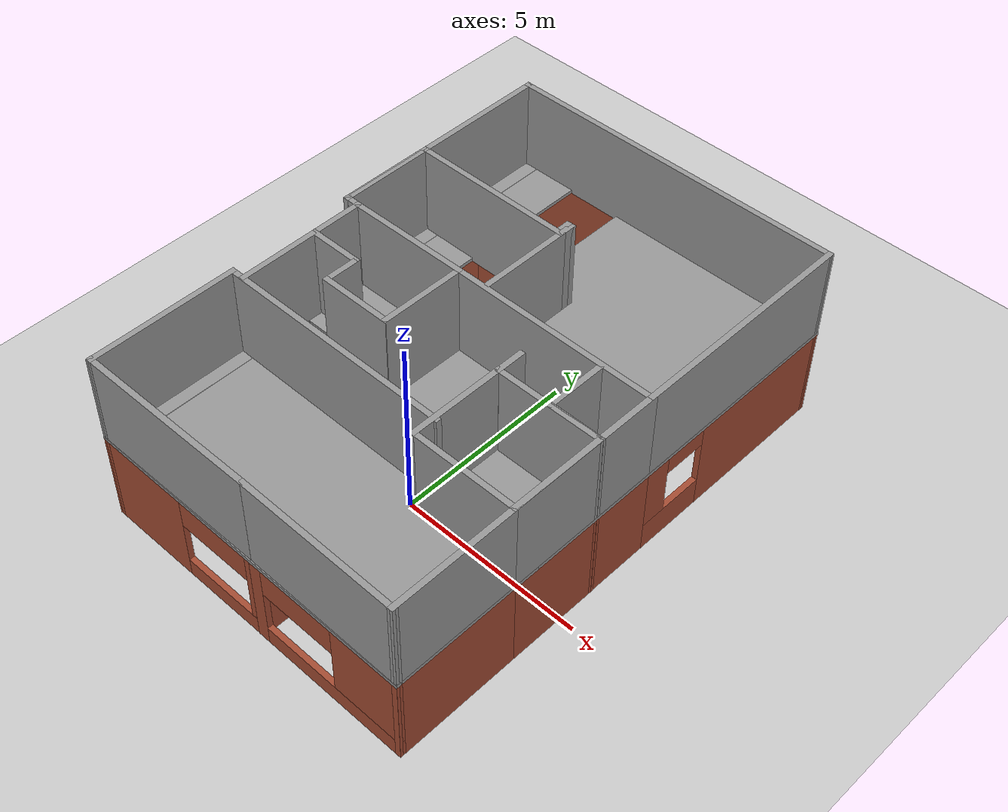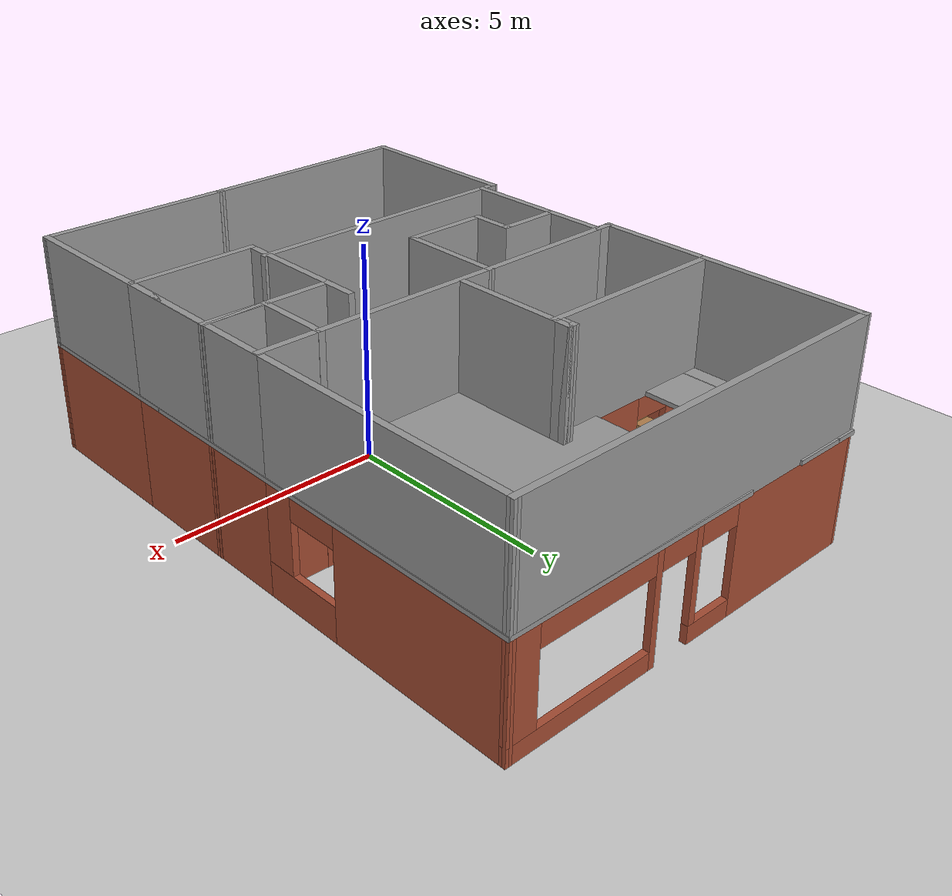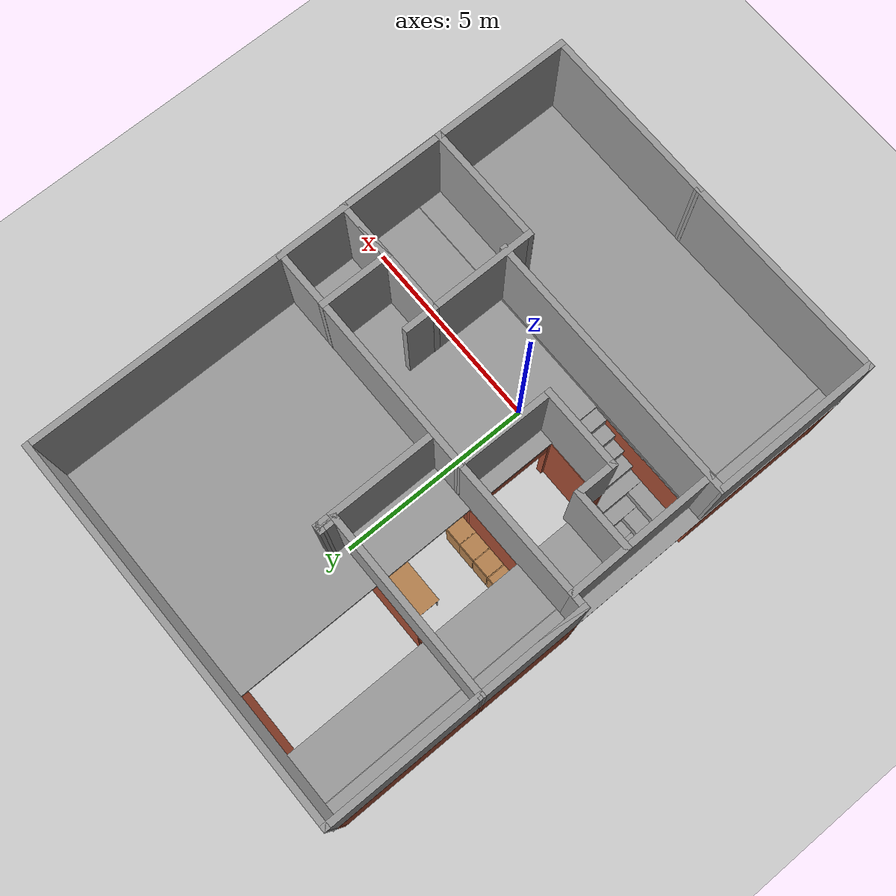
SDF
<sdf version="1.7">
 <world name="default">
  <light name="sun" type="directional">
   <pose>0 0 10 0 -0 0</pose>
   <diffuse>0.8 0.8 0.8 1</diffuse>
   <specular>0.2 0.2 0.2 1</specular>
   <attenuation>
    <range>1000</range>
    <constant>0.9</constant>
    <linear>0.01</linear>
    <quadratic>0.001</quadratic>
   </attenuation>
   <direction>-0.5 0.1 -0.9</direction>
   <spot><inner_angle>0</inner_angle><outer_angle>0</outer_angle><falloff>0</falloff></spot>
  </light>
  <model name="ground_plane">
   <static>1</static>
   <link name="link">
    <collision name="collision">
     <geometry><plane><normal>0 0 1</normal><size>100 100</size></plane></geometry>
     <surface><friction><ode><mu>100</mu><mu2>50</mu2></ode></friction></surface>
    </collision>
    <visual name="visual">
     <cast_shadows>0</cast_shadows>
     <geometry><plane><normal>0 0 1</normal><size>100 100</size></plane></geometry>
     <material>
      <script><uri>file://media/materials/scripts/gazebo.material</uri><name>Gazebo/Grey</name></script>
     </material>
    </visual>
   </link>
  </model>
  <gravity>0 0 -9.8</gravity>
  <magnetic_field>6e-06 2.3e-05 -4.2e-05</magnetic_field>
  <atmosphere type="adiabatic"/>
  <physics type="ode">
   <max_step_size>0.001</max_step_size>
   <real_time_factor>1</real_time_factor>
   <real_time_update_rate>1000</real_time_update_rate>
  </physics>
  <scene><ambient>0.4 0.4 0.4 1</ambient><background>0.7 0.7 0.7 1</background><shadows>1</shadows></scene>
  <audio><device>default</device></audio>
  <spherical_coordinates>
   <surface_model>EARTH_WGS84</surface_model>
   <latitude_deg>0</latitude_deg>
   <longitude_deg>0</longitude_deg>
   <elevation>0</elevation>
   <heading_deg>0</heading_deg>
  </spherical_coordinates>
  <model name="ZuHause">
   <pose>0.001955 2.012 0 0 -0 0</pose>
   <link name="Floor_2">
    <pose>0.000206 -0.000134 2.5 0 -0 0</pose>
    <visual name="Floor_2_Visual_0">
     <pose>-4.38196 0 0.05 0 -0 0</pose>
     <geometry><box><size>0.503546 13.6275 0.1</size></box></geometry>
     <material>
      <script><uri>file://media/materials/scripts/gazebo.material</uri><name>Gazebo/Grey</name></script>
      <ambient>1 1 1 1</ambient>
     </material>
     <meta><layer>1</layer></meta>
    </visual>
    <collision name="Floor_2_Collision_0">
     <geometry><box><size>0.503546 13.6275 0.1</size></box></geometry>
     <pose>-4.38196 0 0.05 0 -0 0</pose>
    </collision>
    <visual name="Floor_2_Visual_1">
     <pose>-4.12306 -4.79997 0.05 0 -0 0</pose>
     <geometry><box><size>0.014263 4.02759 0.1</size></box></geometry>
     <material>
      <script><uri>file://media/materials/scripts/gazebo.material</uri><name>Gazebo/Grey</name></script>
      <ambient>1 1 1 1</ambient>
     </material>
     <meta><layer>1</layer></meta>
    </visual>
    <collision name="Floor_2_Collision_1">
     <geometry><box><size>0.014263 4.02759 0.1</size></box></geometry>
     <pose>-4.12306 -4.79997 0.05 0 -0 0</pose>
    </collision>
    <visual name="Floor_2_Visual_2">
     <pose>0.258905 -4.80487 0.05 0 -0 0</pose>
     <geometry><box><size>8.74967 4.01778 0.1</size></box></geometry>
     <material>
      <script><uri>file://media/materials/scripts/gazebo.material</uri><name>Gazebo/Grey</name></script>
      <ambient>1 1 1 1</ambient>
     </material>
     <meta><layer>1</layer></meta>
    </visual>
    <collision name="Floor_2_Collision_2">
     <geometry><box><size>8.74967 4.01778 0.1</size></box></geometry>
     <pose>0.258905 -4.80487 0.05 0 -0 0</pose>
    </collision>
    <visual name="Floor_2_Visual_3">
     <pose>0.858905 -2.79108 0.05 0 -0 0</pose>
     <geometry><box><size>7.54967 0.009809 0.1</size></box></geometry>
     <material>
      <script><uri>file://media/materials/scripts/gazebo.material</uri><name>Gazebo/Grey</name></script>
      <ambient>1 1 1 1</ambient>
     </material>
     <meta><layer>1</layer></meta>
    </visual>
    <collision name="Floor_2_Collision_3">
     <geometry><box><size>7.54967 0.009809 0.1</size></box></geometry>
     <pose>0.858905 -2.79108 0.05 0 -0 0</pose>
    </collision>
    <visual name="Floor_2_Visual_4">
     <pose>1.5995 2.01379 0.05 0 -0 0</pose>
     <geometry><box><size>6.06847 9.59994 0.1</size></box></geometry>
     <material>
      <script><uri>file://media/materials/scripts/gazebo.material</uri><name>Gazebo/Grey</name></script>
      <ambient>1 1 1 1</ambient>
     </material>
     <meta><layer>1</layer></meta>
    </visual>
    <collision name="Floor_2_Collision_4">
     <geometry><box><size>6.06847 9.59994 0.1</size></box></geometry>
     <pose>1.5995 2.01379 0.05 0 -0 0</pose>
    </collision>
    <visual name="Floor_2_Visual_5">
     <pose>-4.12306 2.56379 0.05 0 -0 0</pose>
     <geometry><box><size>0.014263 8.49994 0.1</size></box></geometry>
     <material>
      <script><uri>file://media/materials/scripts/gazebo.material</uri><name>Gazebo/Grey</name></script>
      <ambient>1 1 1 1</ambient>
     </material>
     <meta><layer>1</layer></meta>
    </visual>
    <collision name="Floor_2_Collision_5">
     <geometry><box><size>0.014263 8.49994 0.1</size></box></geometry>
     <pose>-4.12306 2.56379 0.05 0 -0 0</pose>
    </collision>
    <visual name="Floor_2_Visual_6">
     <pose>-3.51593 2.79256 0.05 0 -0 0</pose>
     <geometry><box><size>1.2 8.0424 0.1</size></box></geometry>
     <material>
      <script><uri>file://media/materials/scripts/gazebo.material</uri><name>Gazebo/Grey</name></script>
      <ambient>1 1 1 1</ambient>
     </material>
     <meta><layer>1</layer></meta>
    </visual>
    <collision name="Floor_2_Collision_6">
     <geometry><box><size>1.2 8.0424 0.1</size></box></geometry>
     <pose>-3.51593 2.79256 0.05 0 -0 0</pose>
    </collision>
   </link>
   <link name="Stairs_4">
    <visual name="Stairs_4_Visual_0">
     <pose>-3.51572 -1.42469 0.15 0 -0 0</pose>
     <geometry><box><size>1.2 0.391837 0.3</size></box></geometry>
     <material>
      <script><uri>file://media/materials/scripts/gazebo.material</uri><name>Gazebo/Grey</name></script>
      <ambient>1 1 1 1</ambient>
     </material>
     <meta><layer>0</layer></meta>
    </visual>
    <collision name="Stairs_4_Collision_0">
     <geometry><box><size>1.2 0.391837 0.3</size></box></geometry>
     <pose>-3.51572 -1.42469 0.15 0 -0 0</pose>
    </collision>
    <visual name="Stairs_4_Visual_1">
     <pose>-3.51572 -1.81652 0.45 0 -0 0</pose>
     <geometry><box><size>1.2 0.391837 0.3</size></box></geometry>
     <material>
      <script><uri>file://media/materials/scripts/gazebo.material</uri><name>Gazebo/Grey</name></script>
      <ambient>1 1 1 1</ambient>
     </material>
     <meta><layer>0</layer></meta>
    </visual>
    <collision name="Stairs_4_Collision_1">
     <geometry><box><size>1.2 0.391837 0.3</size></box></geometry>
     <pose>-3.51572 -1.81652 0.45 0 -0 0</pose>
    </collision>
    <visual name="Stairs_4_Visual_2">
     <pose>-3.51572 -2.20836 0.75 0 -0 0</pose>
     <geometry><box><size>1.2 0.391837 0.3</size></box></geometry>
     <material>
      <script><uri>file://media/materials/scripts/gazebo.material</uri><name>Gazebo/Grey</name></script>
      <ambient>1 1 1 1</ambient>
     </material>
     <meta><layer>0</layer></meta>
    </visual>
    <collision name="Stairs_4_Collision_2">
     <geometry><box><size>1.2 0.391837 0.3</size></box></geometry>
     <pose>-3.51572 -2.20836 0.75 0 -0 0</pose>
    </collision>
    <visual name="Stairs_4_Visual_3">
     <pose>-3.51572 -2.6002 1.05 0 -0 0</pose>
     <geometry><box><size>1.2 0.391837 0.3</size></box></geometry>
     <material>
      <script><uri>file://media/materials/scripts/gazebo.material</uri><name>Gazebo/Grey</name></script>
      <ambient>1 1 1 1</ambient>
     </material>
     <meta><layer>0</layer></meta>
    </visual>
    <collision name="Stairs_4_Collision_3">
     <geometry><box><size>1.2 0.391837 0.3</size></box></geometry>
     <pose>-3.51572 -2.6002 1.05 0 -0 0</pose>
    </collision>
   </link>
   <link name="Stairs_6">
    <visual name="Stairs_6_Visual_0">
     <pose>-3.96152 -2.23631 0.15625 0 -0 1.5708</pose>
     <geometry><box><size>1.1 0.336932 0.3125</size></box></geometry>
     <material>
      <script><uri>file://media/materials/scripts/gazebo.material</uri><name>Gazebo/Grey</name></script>
      <ambient>1 1 1 1</ambient>
     </material>
     <meta><layer>0</layer></meta>
    </visual>
    <collision name="Stairs_6_Collision_0">
     <geometry><box><size>1.1 0.336932 0.3125</size></box></geometry>
     <pose>-3.96152 -2.23631 0.15625 0 -0 1.5708</pose>
    </collision>
    <visual name="Stairs_6_Visual_1">
     <pose>-3.62459 -2.23631 0.46875 0 -0 1.5708</pose>
     <geometry><box><size>1.1 0.336932 0.3125</size></box></geometry>
     <material>
      <script><uri>file://media/materials/scripts/gazebo.material</uri><name>Gazebo/Grey</name></script>
      <ambient>1 1 1 1</ambient>
     </material>
     <meta><layer>0</layer></meta>
    </visual>
    <collision name="Stairs_6_Collision_1">
     <geometry><box><size>1.1 0.336932 0.3125</size></box></geometry>
     <pose>-3.62459 -2.23631 0.46875 0 -0 1.5708</pose>
    </collision>
    <visual name="Stairs_6_Visual_2">
     <pose>-3.28765 -2.23631 0.78125 0 -0 1.5708</pose>
     <geometry><box><size>1.1 0.336932 0.3125</size></box></geometry>
     <material>
      <script><uri>file://media/materials/scripts/gazebo.material</uri><name>Gazebo/Grey</name></script>
      <ambient>1 1 1 1</ambient>
     </material>
     <meta><layer>0</layer></meta>
    </visual>
    <collision name="Stairs_6_Collision_2">
     <geometry><box><size>1.1 0.336932 0.3125</size></box></geometry>
     <pose>-3.28765 -2.23631 0.78125 0 -0 1.5708</pose>
    </collision>
    <visual name="Stairs_6_Visual_3">
     <pose>-2.95072 -2.23631 1.09375 0 -0 1.5708</pose>
     <geometry><box><size>1.1 0.336932 0.3125</size></box></geometry>
     <material>
      <script><uri>file://media/materials/scripts/gazebo.material</uri><name>Gazebo/Grey</name></script>
      <ambient>1 1 1 1</ambient>
     </material>
     <meta><layer>0</layer></meta>
    </visual>
    <collision name="Stairs_6_Collision_3">
     <geometry><box><size>1.1 0.336932 0.3125</size></box></geometry>
     <pose>-2.95072 -2.23631 1.09375 0 -0 1.5708</pose>
    </collision>
    <visual name="Stairs_6_Visual_4">
     <pose>-2.61379 -2.23631 1.40625 0 -0 1.5708</pose>
     <geometry><box><size>1.1 0.336932 0.3125</size></box></geometry>
     <material>
      <script><uri>file://media/materials/scripts/gazebo.material</uri><name>Gazebo/Grey</name></script>
      <ambient>1 1 1 1</ambient>
     </material>
     <meta><layer>0</layer></meta>
    </visual>
    <collision name="Stairs_6_Collision_4">
     <geometry><box><size>1.1 0.336932 0.3125</size></box></geometry>
     <pose>-2.61379 -2.23631 1.40625 0 -0 1.5708</pose>
    </collision>
    <visual name="Stairs_6_Visual_5">
     <pose>-2.27686 -2.23631 1.71875 0 -0 1.5708</pose>
     <geometry><box><size>1.1 0.336932 0.3125</size></box></geometry>
     <material>
      <script><uri>file://media/materials/scripts/gazebo.material</uri><name>Gazebo/Grey</name></script>
      <ambient>1 1 1 1</ambient>
     </material>
     <meta><layer>0</layer></meta>
    </visual>
    <collision name="Stairs_6_Collision_5">
     <geometry><box><size>1.1 0.336932 0.3125</size></box></geometry>
     <pose>-2.27686 -2.23631 1.71875 0 -0 1.5708</pose>
    </collision>
    <visual name="Stairs_6_Visual_6">
     <pose>-1.93993 -2.23631 2.03125 0 -0 1.5708</pose>
     <geometry><box><size>1.1 0.336932 0.3125</size></box></geometry>
     <material>
      <script><uri>file://media/materials/scripts/gazebo.material</uri><name>Gazebo/Grey</name></script>
      <ambient>1 1 1 1</ambient>
     </material>
     <meta><layer>0</layer></meta>
    </visual>
    <collision name="Stairs_6_Collision_6">
     <geometry><box><size>1.1 0.336932 0.3125</size></box></geometry>
     <pose>-1.93993 -2.23631 2.03125 0 -0 1.5708</pose>
    </collision>
    <visual name="Stairs_6_Visual_7">
     <pose>-1.60299 -2.23631 2.34375 0 -0 1.5708</pose>
     <geometry><box><size>1.1 0.336932 0.3125</size></box></geometry>
     <material>
      <script><uri>file://media/materials/scripts/gazebo.material</uri><name>Gazebo/Grey</name></script>
      <ambient>1 1 1 1</ambient>
     </material>
     <meta><layer>0</layer></meta>
    </visual>
    <collision name="Stairs_6_Collision_7">
     <geometry><box><size>1.1 0.336932 0.3125</size></box></geometry>
     <pose>-1.60299 -2.23631 2.34375 0 -0 1.5708</pose>
    </collision>
   </link>
   <link name="Wall_100">
    <collision name="Wall_100_Collision">
     <geometry><box><size>3.75 0.15 2.5</size></box></geometry>
     <pose>0 0 1.25 0 -0 0</pose>
    </collision>
    <visual name="Wall_100_Visual">
     <pose>0 0 1.25 0 -0 0</pose>
     <geometry><box><size>3.75 0.15 2.5</size></box></geometry>
     <material>
      <script><uri>file://media/materials/scripts/gazebo.material</uri><name>Gazebo/Bricks</name></script>
      <ambient>1 1 1 1</ambient>
     </material>
     <meta><layer>0</layer></meta>
    </visual>
    <pose>-4.55586 4.88489 0 0 -0 1.5708</pose>
   </link>
   <link name="Wall_101">
    <pose>-0.005313 6.7116 0 0 -0 0.005871</pose>
    <visual name="Wall_101_Visual_0">
     <pose>-2.86108 0 1.25 0 -0 0</pose>
     <geometry><box><size>3.5291 0.15 2.5</size></box></geometry>
     <material>
      <script><uri>file://media/materials/scripts/gazebo.material</uri><name>Gazebo/Bricks</name></script>
      <ambient>1 1 1 1</ambient>
     </material>
     <meta><layer>0</layer></meta>
    </visual>
    <collision name="Wall_101_Collision_0">
     <geometry><box><size>3.5291 0.15 2.5</size></box></geometry>
     <pose>-2.86108 0 1.25 0 -0 0</pose>
    </collision>
    <visual name="Wall_101_Visual_1">
     <pose>1.05138 0 1.25 0 -0 0</pose>
     <geometry><box><size>0.161287 0.15 2.5</size></box></geometry>
     <material>
      <script><uri>file://media/materials/scripts/gazebo.material</uri><name>Gazebo/Bricks</name></script>
      <ambient>1 1 1 1</ambient>
     </material>
     <meta><layer>0</layer></meta>
    </visual>
    <collision name="Wall_101_Collision_1">
     <geometry><box><size>0.161287 0.15 2.5</size></box></geometry>
     <pose>1.05138 0 1.25 0 -0 0</pose>
    </collision>
    <visual name="Wall_101_Visual_2">
     <pose>-0.512894 0 0.2 0 -0 0</pose>
     <geometry><box><size>1.16726 0.15 0.4</size></box></geometry>
     <material>
      <script><uri>file://media/materials/scripts/gazebo.material</uri><name>Gazebo/Bricks</name></script>
      <ambient>1 1 1 1</ambient>
     </material>
     <meta><layer>0</layer></meta>
    </visual>
    <collision name="Wall_101_Collision_2">
     <geometry><box><size>1.16726 0.15 0.4</size></box></geometry>
     <pose>-0.512894 0 0.2 0 -0 0</pose>
    </collision>
    <visual name="Wall_101_Visual_3">
     <pose>2.87882 0 0.2 0 -0 0</pose>
     <geometry><box><size>3.4936 0.15 0.4</size></box></geometry>
     <material>
      <script><uri>file://media/materials/scripts/gazebo.material</uri><name>Gazebo/Bricks</name></script>
      <ambient>1 1 1 1</ambient>
     </material>
     <meta><layer>0</layer></meta>
    </visual>
    <collision name="Wall_101_Collision_3">
     <geometry><box><size>3.4936 0.15 0.4</size></box></geometry>
     <pose>2.87882 0 0.2 0 -0 0</pose>
    </collision>
    <visual name="Wall_101_Visual_4">
     <pose>-0.012894 0 1.45 0 -0 0</pose>
     <geometry><box><size>0.167259 0.15 2.1</size></box></geometry>
     <material>
      <script><uri>file://media/materials/scripts/gazebo.material</uri><name>Gazebo/Bricks</name></script>
      <ambient>1 1 1 1</ambient>
     </material>
     <meta><layer>0</layer></meta>
    </visual>
    <collision name="Wall_101_Collision_4">
     <geometry><box><size>0.167259 0.15 2.1</size></box></geometry>
     <pose>-0.012894 0 1.45 0 -0 0</pose>
    </collision>
    <visual name="Wall_101_Visual_5">
     <pose>-0.012894 0 1.45 0 -0 0</pose>
     <geometry><box><size>0.167259 0.15 2.1</size></box></geometry>
     <material>
      <script><uri>file://media/materials/scripts/gazebo.material</uri><name>Gazebo/Bricks</name></script>
      <ambient>1 1 1 1</ambient>
     </material>
     <meta><layer>0</layer></meta>
    </visual>
    <collision name="Wall_101_Collision_5">
     <geometry><box><size>0.167259 0.15 2.1</size></box></geometry>
     <pose>-0.012894 0 1.45 0 -0 0</pose>
    </collision>
    <visual name="Wall_101_Visual_6">
     <pose>4.27882 0 1.45 0 -0 0</pose>
     <geometry><box><size>0.693604 0.15 2.1</size></box></geometry>
     <material>
      <script><uri>file://media/materials/scripts/gazebo.material</uri><name>Gazebo/Bricks</name></script>
      <ambient>1 1 1 1</ambient>
     </material>
     <meta><layer>0</layer></meta>
    </visual>
    <collision name="Wall_101_Collision_6">
     <geometry><box><size>0.693604 0.15 2.1</size></box></geometry>
     <pose>4.27882 0 1.45 0 -0 0</pose>
    </collision>
    <visual name="Wall_101_Visual_7">
     <pose>0.520735 0 2.25 0 -0 0</pose>
     <geometry><box><size>0.9 0.15 0.5</size></box></geometry>
     <material>
      <script><uri>file://media/materials/scripts/gazebo.material</uri><name>Gazebo/Bricks</name></script>
      <ambient>1 1 1 1</ambient>
     </material>
     <meta><layer>0</layer></meta>
    </visual>
    <collision name="Wall_101_Collision_7">
     <geometry><box><size>0.9 0.15 0.5</size></box></geometry>
     <pose>0.520735 0 2.25 0 -0 0</pose>
    </collision>
    <visual name="Wall_101_Visual_8">
     <pose>0.520735 0 2.25 0 -0 0</pose>
     <geometry><box><size>0.9 0.15 0.5</size></box></geometry>
     <material>
      <script><uri>file://media/materials/scripts/gazebo.material</uri><name>Gazebo/Bricks</name></script>
      <ambient>1 1 1 1</ambient>
     </material>
     <meta><layer>0</layer></meta>
    </visual>
    <collision name="Wall_101_Collision_8">
     <geometry><box><size>0.9 0.15 0.5</size></box></geometry>
     <pose>0.520735 0 2.25 0 -0 0</pose>
    </collision>
    <visual name="Wall_101_Visual_9">
     <pose>-0.596524 0 2.25 0 -0 0</pose>
     <geometry><box><size>1 0.15 0.5</size></box></geometry>
     <material>
      <script><uri>file://media/materials/scripts/gazebo.material</uri><name>Gazebo/Bricks</name></script>
      <ambient>1 1 1 1</ambient>
     </material>
     <meta><layer>0</layer></meta>
    </visual>
    <collision name="Wall_101_Collision_9">
     <geometry><box><size>1 0.15 0.5</size></box></geometry>
     <pose>-0.596524 0 2.25 0 -0 0</pose>
    </collision>
    <visual name="Wall_101_Visual_10">
     <pose>2.53202 0 2.25 0 -0 0</pose>
     <geometry><box><size>2.8 0.15 0.5</size></box></geometry>
     <material>
      <script><uri>file://media/materials/scripts/gazebo.material</uri><name>Gazebo/Bricks</name></script>
      <ambient>1 1 1 1</ambient>
     </material>
     <meta><layer>0</layer></meta>
    </visual>
    <collision name="Wall_101_Collision_10">
     <geometry><box><size>2.8 0.15 0.5</size></box></geometry>
     <pose>2.53202 0 2.25 0 -0 0</pose>
    </collision>
   </link>
   <link name="Wall_102">
    <pose>4.54523 3.68832 0 0 -0 -1.5708</pose>
    <visual name="Wall_102_Visual_0">
     <pose>-1.02307 0 1.25 0 -0 0</pose>
     <geometry><box><size>4.20385 0.15 2.5</size></box></geometry>
     <material>
      <script><uri>file://media/materials/scripts/gazebo.material</uri><name>Gazebo/Bricks</name></script>
      <ambient>1 1 1 1</ambient>
     </material>
     <meta><layer>0</layer></meta>
    </visual>
    <collision name="Wall_102_Collision_0">
     <geometry><box><size>4.20385 0.15 2.5</size></box></geometry>
     <pose>-1.02307 0 1.25 0 -0 0</pose>
    </collision>
    <visual name="Wall_102_Visual_1">
     <pose>2.10193 0 0.4 0 -0 0</pose>
     <geometry><box><size>2.04615 0.15 0.8</size></box></geometry>
     <material>
      <script><uri>file://media/materials/scripts/gazebo.material</uri><name>Gazebo/Bricks</name></script>
      <ambient>1 1 1 1</ambient>
     </material>
     <meta><layer>0</layer></meta>
    </visual>
    <collision name="Wall_102_Collision_1">
     <geometry><box><size>2.04615 0.15 0.8</size></box></geometry>
     <pose>2.10193 0 0.4 0 -0 0</pose>
    </collision>
    <visual name="Wall_102_Visual_2">
     <pose>2.70193 0 1.65 0 -0 0</pose>
     <geometry><box><size>0.84615 0.15 1.7</size></box></geometry>
     <material>
      <script><uri>file://media/materials/scripts/gazebo.material</uri><name>Gazebo/Bricks</name></script>
      <ambient>1 1 1 1</ambient>
     </material>
     <meta><layer>0</layer></meta>
    </visual>
    <collision name="Wall_102_Collision_2">
     <geometry><box><size>0.84615 0.15 1.7</size></box></geometry>
     <pose>2.70193 0 1.65 0 -0 0</pose>
    </collision>
    <visual name="Wall_102_Visual_3">
     <pose>1.67885 0 2.25 0 -0 0</pose>
     <geometry><box><size>1.2 0.15 0.5</size></box></geometry>
     <material>
      <script><uri>file://media/materials/scripts/gazebo.material</uri><name>Gazebo/Bricks</name></script>
      <ambient>1 1 1 1</ambient>
     </material>
     <meta><layer>0</layer></meta>
    </visual>
    <collision name="Wall_102_Collision_3">
     <geometry><box><size>1.2 0.15 0.5</size></box></geometry>
     <pose>1.67885 0 2.25 0 -0 0</pose>
    </collision>
   </link>
   <link name="Wall_104">
    <collision name="Wall_104_Collision">
     <geometry><box><size>0.5 0.15 2.5</size></box></geometry>
     <pose>0 0 1.25 0 -0 0</pose>
    </collision>
    <visual name="Wall_104_Visual">
     <pose>0 0 1.25 0 -0 0</pose>
     <geometry><box><size>0.5 0.15 2.5</size></box></geometry>
     <material>
      <script><uri>file://media/materials/scripts/gazebo.material</uri><name>Gazebo/Bricks</name></script>
      <ambient>1 1 1 1</ambient>
     </material>
     <meta><layer>0</layer></meta>
    </visual>
    <pose>-0.20586 3.25989 0 0 -0 1.5708</pose>
   </link>
   <link name="Wall_105">
    <collision name="Wall_105_Collision">
     <geometry><box><size>0.25 0.15 2.5</size></box></geometry>
     <pose>0 0 1.25 0 -0 0</pose>
    </collision>
    <visual name="Wall_105_Visual">
     <pose>0 0 1.25 0 -0 0</pose>
     <geometry><box><size>0.25 0.15 2.5</size></box></geometry>
     <material>
      <script><uri>file://media/materials/scripts/gazebo.material</uri><name>Gazebo/Bricks</name></script>
      <ambient>1 1 1 1</ambient>
     </material>
     <meta><layer>0</layer></meta>
    </visual>
    <pose>-0.25586 3.43489 0 0 -0 3.14159</pose>
   </link>
   <link name="Wall_106">
    <collision name="Wall_106_Collision">
     <geometry><box><size>0.485068 0.15 2.5</size></box></geometry>
     <pose>0 0 1.25 0 -0 0</pose>
    </collision>
    <visual name="Wall_106_Visual">
     <pose>0 0 1.25 0 -0 0</pose>
     <geometry><box><size>0.485068 0.15 2.5</size></box></geometry>
     <material>
      <script><uri>file://media/materials/scripts/gazebo.material</uri><name>Gazebo/Bricks</name></script>
      <ambient>1 1 1 1</ambient>
     </material>
     <meta><layer>0</layer></meta>
    </visual>
    <pose>-0.305851 3.26736 0 0 -0 -1.57074</pose>
   </link>
   <link name="Wall_108">
    <collision name="Wall_108_Collision">
     <geometry><box><size>2.5 0.15 2.5</size></box></geometry>
     <pose>0 0 1.25 0 -0 0</pose>
    </collision>
    <visual name="Wall_108_Visual">
     <pose>0 0 1.25 0 -0 0</pose>
     <geometry><box><size>2.5 0.15 2.5</size></box></geometry>
     <material>
      <script><uri>file://media/materials/scripts/gazebo.material</uri><name>Gazebo/Grey</name></script>
      <ambient>1 1 1 1</ambient>
     </material>
     <meta><layer>1</layer></meta>
    </visual>
    <pose>-4.55744 1.75088 2.5 0 -0 -1.5708</pose>
   </link>
   <link name="Wall_109">
    <collision name="Wall_109_Collision">
     <geometry><box><size>0.488554 0.15 2.5</size></box></geometry>
     <pose>0 0 1.25 0 -0 0</pose>
    </collision>
    <visual name="Wall_109_Visual">
     <pose>0 0 1.25 0 -0 0</pose>
     <geometry><box><size>0.488554 0.15 2.5</size></box></geometry>
     <material>
      <script><uri>file://media/materials/scripts/gazebo.material</uri><name>Gazebo/Grey</name></script>
      <ambient>1 1 1 1</ambient>
     </material>
     <meta><layer>1</layer></meta>
    </visual>
    <pose>-4.38819 0.578755 2.5 0 -0 -0.016977</pose>
   </link>
   <link name="Wall_110">
    <collision name="Wall_110_Collision">
     <geometry><box><size>3.59527 0.15 2.5</size></box></geometry>
     <pose>0 0 1.25 0 -0 0</pose>
    </collision>
    <visual name="Wall_110_Visual">
     <pose>0 0 1.25 0 -0 0</pose>
     <geometry><box><size>3.59527 0.15 2.5</size></box></geometry>
     <material>
      <script><uri>file://media/materials/scripts/gazebo.material</uri><name>Gazebo/Grey</name></script>
      <ambient>1 1 1 1</ambient>
     </material>
     <meta><layer>1</layer></meta>
    </visual>
    <pose>-4.20835 -1.14672 2.5 0 -0 -1.56465</pose>
   </link>
   <link name="Wall_111">
    <collision name="Wall_111_Collision">
     <geometry><box><size>3.37854 0.15 2.5</size></box></geometry>
     <pose>0 0 1.25 0 -0 0</pose>
    </collision>
    <visual name="Wall_111_Visual">
     <pose>0 0 1.25 0 -0 0</pose>
     <geometry><box><size>3.37854 0.15 2.5</size></box></geometry>
     <material>
      <script><uri>file://media/materials/scripts/gazebo.material</uri><name>Gazebo/Grey</name></script>
      <ambient>1 1 1 1</ambient>
     </material>
     <meta><layer>1</layer></meta>
    </visual>
    <pose>-2.60474 0.591186 2.5 0 -0 0.009481</pose>
   </link>
   <link name="Wall_112">
    <collision name="Wall_112_Collision">
     <geometry><box><size>2.36905 0.15 2.5</size></box></geometry>
     <pose>0 0 1.25 0 -0 0</pose>
    </collision>
    <visual name="Wall_112_Visual">
     <pose>0 0 1.25 0 -0 0</pose>
     <geometry><box><size>2.36905 0.15 2.5</size></box></geometry>
     <material>
      <script><uri>file://media/materials/scripts/gazebo.material</uri><name>Gazebo/Grey</name></script>
      <ambient>1 1 1 1</ambient>
     </material>
     <meta><layer>1</layer></meta>
    </visual>
    <pose>-0.99461 -0.507996 2.5 0 -0 -1.57446</pose>
   </link>
   <link name="Wall_113">
    <collision name="Wall_113_Collision">
     <geometry><box><size>1 0.15 2.5</size></box></geometry>
     <pose>0 0 1.25 0 -0 0</pose>
    </collision>
    <visual name="Wall_113_Visual">
     <pose>0 0 1.25 0 -0 0</pose>
     <geometry><box><size>1 0.15 2.5</size></box></geometry>
     <material>
      <script><uri>file://media/materials/scripts/gazebo.material</uri><name>Gazebo/Grey</name></script>
      <ambient>1 1 1 1</ambient>
     </material>
     <meta><layer>1</layer></meta>
    </visual>
    <pose>-2.8489 -1.19254 2.5 0 -0 -1.5708</pose>
   </link>
   <link name="Wall_114">
    <collision name="Wall_114_Collision">
     <geometry><box><size>2 0.15 2.5</size></box></geometry>
     <pose>0 0 1.25 0 -0 0</pose>
    </collision>
    <visual name="Wall_114_Visual">
     <pose>0 0 1.25 0 -0 0</pose>
     <geometry><box><size>2 0.15 2.5</size></box></geometry>
     <material>
      <script><uri>file://media/materials/scripts/gazebo.material</uri><name>Gazebo/Grey</name></script>
      <ambient>1 1 1 1</ambient>
     </material>
     <meta><layer>1</layer></meta>
    </visual>
    <pose>-1.9239 -1.62325 2.5 0 -0 0</pose>
   </link>
   <link name="Wall_115">
    <collision name="Wall_115_Collision">
     <geometry><box><size>5.65913 0.15 2.5</size></box></geometry>
     <pose>0 0 1.25 0 -0 0</pose>
    </collision>
    <visual name="Wall_115_Visual">
     <pose>0 0 1.25 0 -0 0</pose>
     <geometry><box><size>5.65913 0.15 2.5</size></box></geometry>
     <material>
      <script><uri>file://media/materials/scripts/gazebo.material</uri><name>Gazebo/Grey</name></script>
      <ambient>1 1 1 1</ambient>
     </material>
     <meta><layer>1</layer></meta>
    </visual>
    <pose>1.76402 0.60649 2.5 0 -0 0</pose>
   </link>
   <link name="Wall_116">
    <collision name="Wall_116_Collision">
     <geometry><box><size>6.5 0.15 2.5</size></box></geometry>
     <pose>0 0 1.25 0 -0 0</pose>
    </collision>
    <visual name="Wall_116_Visual">
     <pose>0 0 1.25 0 -0 0</pose>
     <geometry><box><size>6.5 0.15 2.5</size></box></geometry>
     <material>
      <script><uri>file://media/materials/scripts/gazebo.material</uri><name>Gazebo/Grey</name></script>
      <ambient>1 1 1 1</ambient>
     </material>
     <meta><layer>1</layer></meta>
    </visual>
    <pose>-1.35316 -2.88854 2.5 0 -0 3.14159</pose>
   </link>
   <link name="Wall_117">
    <collision name="Wall_117_Collision">
     <geometry><box><size>4 0.15 2.5</size></box></geometry>
     <pose>0 0 1.25 0 -0 0</pose>
    </collision>
    <visual name="Wall_117_Visual">
     <pose>0 0 1.25 0 -0 0</pose>
     <geometry><box><size>4 0.15 2.5</size></box></geometry>
     <material>
      <script><uri>file://media/materials/scripts/gazebo.material</uri><name>Gazebo/Grey</name></script>
      <ambient>1 1 1 1</ambient>
     </material>
     <meta><layer>1</layer></meta>
    </visual>
    <pose>-4.53674 -4.81354 2.5 0 -0 -1.57158</pose>
   </link>
   <link name="Wall_118">
    <collision name="Wall_118_Collision">
     <geometry><box><size>5.00002 0.15 2.5</size></box></geometry>
     <pose>0 0 1.25 0 -0 0</pose>
    </collision>
    <visual name="Wall_118_Visual">
     <pose>0 0 1.25 0 -0 0</pose>
     <geometry><box><size>5.00002 0.15 2.5</size></box></geometry>
     <material>
      <script><uri>file://media/materials/scripts/gazebo.material</uri><name>Gazebo/Grey</name></script>
      <ambient>1 1 1 1</ambient>
     </material>
     <meta><layer>1</layer></meta>
    </visual>
    <pose>-2.12032 -6.72278 2.5 0 -0 0.006499</pose>
   </link>
   <link name="Wall_120">
    <collision name="Wall_120_Collision">
     <geometry><box><size>4.40395 0.15 2.5</size></box></geometry>
     <pose>0 0 1.25 0 -0 0</pose>
    </collision>
    <visual name="Wall_120_Visual">
     <pose>0 0 1.25 0 -0 0</pose>
     <geometry><box><size>4.40395 0.15 2.5</size></box></geometry>
     <material>
      <script><uri>file://media/materials/scripts/gazebo.material</uri><name>Gazebo/Grey</name></script>
      <ambient>1 1 1 1</ambient>
     </material>
     <meta><layer>1</layer></meta>
    </visual>
    <pose>2.43165 -6.7211 2.5 0 -0 -0.006621</pose>
   </link>
   <link name="Wall_122">
    <collision name="Wall_122_Collision">
     <geometry><box><size>3.42352 0.15 2.5</size></box></geometry>
     <pose>0 0 1.25 0 -0 0</pose>
    </collision>
    <visual name="Wall_122_Visual">
     <pose>0 0 1.25 0 -0 0</pose>
     <geometry><box><size>3.42352 0.15 2.5</size></box></geometry>
     <material>
      <script><uri>file://media/materials/scripts/gazebo.material</uri><name>Gazebo/Grey</name></script>
      <ambient>1 1 1 1</ambient>
     </material>
     <meta><layer>1</layer></meta>
    </visual>
    <pose>4.55523 -5.09843 2.5 0 -0 1.57287</pose>
   </link>
   <link name="Wall_123">
    <collision name="Wall_123_Collision">
     <geometry><box><size>2.94648 0.15 2.5</size></box></geometry>
     <pose>0 0 1.25 0 -0 0</pose>
    </collision>
    <visual name="Wall_123_Visual">
     <pose>0 0 1.25 0 -0 0</pose>
     <geometry><box><size>2.94648 0.15 2.5</size></box></geometry>
     <material>
      <script><uri>file://media/materials/scripts/gazebo.material</uri><name>Gazebo/Grey</name></script>
      <ambient>1 1 1 1</ambient>
     </material>
     <meta><layer>1</layer></meta>
    </visual>
    <pose>3.1536 -3.46176 2.5 0 -0 -3.14153</pose>
   </link>
   <link name="Wall_124">
    <collision name="Wall_124_Collision">
     <geometry><box><size>2.5 0.15 2.5</size></box></geometry>
     <pose>0 0 1.25 0 -0 0</pose>
    </collision>
    <visual name="Wall_124_Visual">
     <pose>0 0 1.25 0 -0 0</pose>
     <geometry><box><size>2.5 0.15 2.5</size></box></geometry>
     <material>
      <script><uri>file://media/materials/scripts/gazebo.material</uri><name>Gazebo/Grey</name></script>
      <ambient>1 1 1 1</ambient>
     </material>
     <meta><layer>1</layer></meta>
    </visual>
    <pose>1.75536 -2.28685 2.5 0 -0 1.5708</pose>
   </link>
   <link name="Wall_125">
    <collision name="Wall_125_Collision">
     <geometry><box><size>4.25 0.15 2.5</size></box></geometry>
     <pose>0 0 1.25 0 -0 0</pose>
    </collision>
    <visual name="Wall_125_Visual">
     <pose>0 0 1.25 0 -0 0</pose>
     <geometry><box><size>4.25 0.15 2.5</size></box></geometry>
     <material>
      <script><uri>file://media/materials/scripts/gazebo.material</uri><name>Gazebo/Grey</name></script>
      <ambient>1 1 1 1</ambient>
     </material>
     <meta><layer>1</layer></meta>
    </visual>
    <pose>4.54523 -1.41168 2.5 0 -0 1.5708</pose>
   </link>
   <link name="Wall_126">
    <collision name="Wall_126_Collision">
     <geometry><box><size>2.62506 0.15 2.5</size></box></geometry>
     <pose>0 0 1.25 0 -0 0</pose>
    </collision>
    <visual name="Wall_126_Visual">
     <pose>0 0 1.25 0 -0 0</pose>
     <geometry><box><size>2.62506 0.15 2.5</size></box></geometry>
     <material>
      <script><uri>file://media/materials/scripts/gazebo.material</uri><name>Gazebo/Grey</name></script>
      <ambient>1 1 1 1</ambient>
     </material>
     <meta><layer>1</layer></meta>
    </visual>
    <pose>4.55309 -2.22415 2.5 0 -0 1.56979</pose>
   </link>
   <link name="Wall_127">
    <collision name="Wall_127_Collision">
     <geometry><box><size>2.94945 0.15 2.5</size></box></geometry>
     <pose>0 0 1.25 0 -0 0</pose>
    </collision>
    <visual name="Wall_127_Visual">
     <pose>0 0 1.25 0 -0 0</pose>
     <geometry><box><size>2.94945 0.15 2.5</size></box></geometry>
     <material>
      <script><uri>file://media/materials/scripts/gazebo.material</uri><name>Gazebo/Grey</name></script>
      <ambient>1 1 1 1</ambient>
     </material>
     <meta><layer>1</layer></meta>
    </visual>
    <pose>3.15462 -0.994831 2.5 0 -0 -3.13844</pose>
   </link>
   <link name="Wall_128">
    <collision name="Wall_128_Collision">
     <geometry><box><size>1.5 0.15 2.5</size></box></geometry>
     <pose>0 0 1.25 0 -0 0</pose>
    </collision>
    <visual name="Wall_128_Visual">
     <pose>0 0 1.25 0 -0 0</pose>
     <geometry><box><size>1.5 0.15 2.5</size></box></geometry>
     <material>
      <script><uri>file://media/materials/scripts/gazebo.material</uri><name>Gazebo/Grey</name></script>
      <ambient>1 1 1 1</ambient>
     </material>
     <meta><layer>1</layer></meta>
    </visual>
    <pose>3.87934 -0.990423 2.5 0 -0 3.14159</pose>
   </link>
   <link name="Wall_129">
    <collision name="Wall_129_Collision">
     <geometry><box><size>1.75 0.15 2.5</size></box></geometry>
     <pose>0 0 1.25 0 -0 0</pose>
    </collision>
    <visual name="Wall_129_Visual">
     <pose>0 0 1.25 0 -0 0</pose>
     <geometry><box><size>1.75 0.15 2.5</size></box></geometry>
     <material>
      <script><uri>file://media/materials/scripts/gazebo.material</uri><name>Gazebo/Grey</name></script>
      <ambient>1 1 1 1</ambient>
     </material>
     <meta><layer>1</layer></meta>
    </visual>
    <pose>3.20433 -0.190423 2.5 0 -0 1.5708</pose>
   </link>
   <link name="Wall_130">
    <collision name="Wall_130_Collision">
     <geometry><box><size>0.814945 0.15 2.5</size></box></geometry>
     <pose>0 0 1.25 0 -0 0</pose>
    </collision>
    <visual name="Wall_130_Visual">
     <pose>0 0 1.25 0 -0 0</pose>
     <geometry><box><size>0.814945 0.15 2.5</size></box></geometry>
     <material>
      <script><uri>file://media/materials/scripts/gazebo.material</uri><name>Gazebo/Grey</name></script>
      <ambient>1 1 1 1</ambient>
     </material>
     <meta><layer>1</layer></meta>
    </visual>
    <pose>1.75865 -0.666766 2.5 0 -0 1.57258</pose>
   </link>
   <link name="Wall_131">
    <collision name="Wall_131_Collision">
     <geometry><box><size>2.65326 0.15 2.5</size></box></geometry>
     <pose>0 0 1.25 0 -0 0</pose>
    </collision>
    <visual name="Wall_131_Visual">
     <pose>0 0 1.25 0 -0 0</pose>
     <geometry><box><size>2.65326 0.15 2.5</size></box></geometry>
     <material>
      <script><uri>file://media/materials/scripts/gazebo.material</uri><name>Gazebo/Grey</name></script>
      <ambient>1 1 1 1</ambient>
     </material>
     <meta><layer>1</layer></meta>
    </visual>
    <pose>-4.55665 1.83326 2.5 0 -0 1.57017</pose>
   </link>
   <link name="Wall_132">
    <collision name="Wall_132_Collision">
     <geometry><box><size>4.5 0.15 2.5</size></box></geometry>
     <pose>0 0 1.25 0 -0 0</pose>
    </collision>
    <visual name="Wall_132_Visual">
     <pose>0 0 1.25 0 -0 0</pose>
     <geometry><box><size>4.5 0.15 2.5</size></box></geometry>
     <material>
      <script><uri>file://media/materials/scripts/gazebo.material</uri><name>Gazebo/Grey</name></script>
      <ambient>1 1 1 1</ambient>
     </material>
     <meta><layer>1</layer></meta>
    </visual>
    <pose>-2.38086 3.08489 2.5 0 -0 0</pose>
   </link>
   <link name="Wall_133">
    <collision name="Wall_133_Collision">
     <geometry><box><size>2.5 0.15 2.5</size></box></geometry>
     <pose>0 0 1.25 0 -0 0</pose>
    </collision>
    <visual name="Wall_133_Visual">
     <pose>0 0 1.25 0 -0 0</pose>
     <geometry><box><size>2.5 0.15 2.5</size></box></geometry>
     <material>
      <script><uri>file://media/materials/scripts/gazebo.material</uri><name>Gazebo/Grey</name></script>
      <ambient>1 1 1 1</ambient>
     </material>
     <meta><layer>1</layer></meta>
    </visual>
    <pose>-0.20586 1.90989 2.5 0 -0 -1.5708</pose>
   </link>
   <link name="Wall_134">
    <collision name="Wall_134_Collision">
     <geometry><box><size>3.75 0.15 2.5</size></box></geometry>
     <pose>0 0 1.25 0 -0 0</pose>
    </collision>
    <visual name="Wall_134_Visual">
     <pose>0 0 1.25 0 -0 0</pose>
     <geometry><box><size>3.75 0.15 2.5</size></box></geometry>
     <material>
      <script><uri>file://media/materials/scripts/gazebo.material</uri><name>Gazebo/Grey</name></script>
      <ambient>1 1 1 1</ambient>
     </material>
     <meta><layer>1</layer></meta>
    </visual>
    <pose>-4.55586 4.88489 2.5 0 -0 1.5708</pose>
   </link>
   <link name="Wall_135">
    <collision name="Wall_135_Collision">
     <geometry><box><size>9.25125 0.15 2.5</size></box></geometry>
     <pose>0 0 1.25 0 -0 0</pose>
    </collision>
    <visual name="Wall_135_Visual">
     <pose>0 0 1.25 0 -0 0</pose>
     <geometry><box><size>9.25125 0.15 2.5</size></box></geometry>
     <material>
      <script><uri>file://media/materials/scripts/gazebo.material</uri><name>Gazebo/Grey</name></script>
      <ambient>1 1 1 1</ambient>
     </material>
     <meta><layer>1</layer></meta>
    </visual>
    <pose>-0.005313 6.7116 2.5 0 -0 0.005871</pose>
   </link>
   <link name="Wall_136">
    <collision name="Wall_136_Collision">
     <geometry><box><size>6.25 0.15 2.5</size></box></geometry>
     <pose>0 0 1.25 0 -0 0</pose>
    </collision>
    <visual name="Wall_136_Visual">
     <pose>0 0 1.25 0 -0 0</pose>
     <geometry><box><size>6.25 0.15 2.5</size></box></geometry>
     <material>
      <script><uri>file://media/materials/scripts/gazebo.material</uri><name>Gazebo/Grey</name></script>
      <ambient>1 1 1 1</ambient>
     </material>
     <meta><layer>1</layer></meta>
    </visual>
    <pose>4.54523 3.68832 2.5 0 -0 -1.5708</pose>
   </link>
   <link name="Wall_137">
    <collision name="Wall_137_Collision">
     <geometry><box><size>0.5 0.15 2.5</size></box></geometry>
     <pose>0 0 1.25 0 -0 0</pose>
    </collision>
    <visual name="Wall_137_Visual">
     <pose>0 0 1.25 0 -0 0</pose>
     <geometry><box><size>0.5 0.15 2.5</size></box></geometry>
     <material>
      <script><uri>file://media/materials/scripts/gazebo.material</uri><name>Gazebo/Grey</name></script>
      <ambient>1 1 1 1</ambient>
     </material>
     <meta><layer>1</layer></meta>
    </visual>
    <pose>-0.20586 3.25989 2.5 0 -0 1.5708</pose>
   </link>
   <link name="Wall_138">
    <collision name="Wall_138_Collision">
     <geometry><box><size>0.25 0.15 2.5</size></box></geometry>
     <pose>0 0 1.25 0 -0 0</pose>
    </collision>
    <visual name="Wall_138_Visual">
     <pose>0 0 1.25 0 -0 0</pose>
     <geometry><box><size>0.25 0.15 2.5</size></box></geometry>
     <material>
      <script><uri>file://media/materials/scripts/gazebo.material</uri><name>Gazebo/Grey</name></script>
      <ambient>1 1 1 1</ambient>
     </material>
     <meta><layer>1</layer></meta>
    </visual>
    <pose>-0.25586 3.43489 2.5 0 -0 3.14159</pose>
   </link>
   <link name="Wall_139">
    <collision name="Wall_139_Collision">
     <geometry><box><size>0.485061 0.15 2.5</size></box></geometry>
     <pose>0 0 1.25 0 -0 0</pose>
    </collision>
    <visual name="Wall_139_Visual">
     <pose>0 0 1.25 0 -0 0</pose>
     <geometry><box><size>0.485061 0.15 2.5</size></box></geometry>
     <material>
      <script><uri>file://media/materials/scripts/gazebo.material</uri><name>Gazebo/Grey</name></script>
      <ambient>1 1 1 1</ambient>
     </material>
     <meta><layer>1</layer></meta>
    </visual>
    <pose>-0.305851 3.26736 2.5 0 -0 -1.57074</pose>
   </link>
   <link name="Wall_140">
    <collision name="Wall_140_Collision">
     <geometry><box><size>1.5 0.15 2.5</size></box></geometry>
     <pose>0 0 1.25 0 -0 0</pose>
    </collision>
    <visual name="Wall_140_Visual">
     <pose>0 0 1.25 0 -0 0</pose>
     <geometry><box><size>1.5 0.15 2.5</size></box></geometry>
     <material>
      <script><uri>file://media/materials/scripts/gazebo.material</uri><name>Gazebo/Grey</name></script>
      <ambient>1 1 1 1</ambient>
     </material>
     <meta><layer>1</layer></meta>
    </visual>
    <pose>-3.5239 -0.767536 2.5 0 -0 3.14159</pose>
   </link>
   <link name="Wall_15">
    <collision name="Wall_15_Collision">
     <geometry><box><size>3.03069 0.15 2.5</size></box></geometry>
     <pose>0 0 1.25 0 -0 0</pose>
    </collision>
    <visual name="Wall_15_Visual">
     <pose>0 0 1.25 0 -0 0</pose>
     <geometry><box><size>3.03069 0.15 2.5</size></box></geometry>
     <material>
      <script><uri>file://media/materials/scripts/gazebo.material</uri><name>Gazebo/Bricks</name></script>
      <ambient>1 1 1 1</ambient>
     </material>
     <meta><layer>0</layer></meta>
    </visual>
    <pose>-2.77867 0.591186 0 0 -0 0.010626</pose>
   </link>
   <link name="Wall_16">
    <pose>-1.34308 -1.1352 0 0 -0 -1.57348</pose>
    <visual name="Wall_16_Visual_0">
     <pose>-1.70399 0 1.25 0 -0 0</pose>
     <geometry><box><size>0.225416 0.15 2.5</size></box></geometry>
     <material>
      <script><uri>file://media/materials/scripts/gazebo.material</uri><name>Gazebo/Bricks</name></script>
      <ambient>1 1 1 1</ambient>
     </material>
     <meta><layer>0</layer></meta>
    </visual>
    <collision name="Wall_16_Collision_0">
     <geometry><box><size>0.225416 0.15 2.5</size></box></geometry>
     <pose>-1.70399 0 1.25 0 -0 0</pose>
    </collision>
    <visual name="Wall_16_Visual_1">
     <pose>1.07237 0 1.25 0 -0 0</pose>
     <geometry><box><size>1.48864 0.15 2.5</size></box></geometry>
     <material>
      <script><uri>file://media/materials/scripts/gazebo.material</uri><name>Gazebo/Bricks</name></script>
      <ambient>1 1 1 1</ambient>
     </material>
     <meta><layer>0</layer></meta>
    </visual>
    <collision name="Wall_16_Collision_1">
     <geometry><box><size>1.48864 0.15 2.5</size></box></geometry>
     <pose>1.07237 0 1.25 0 -0 0</pose>
    </collision>
    <visual name="Wall_16_Visual_2">
     <pose>-0.631614 0 2.25 0 -0 0</pose>
     <geometry><box><size>1.91933 0.15 0.5</size></box></geometry>
     <material>
      <script><uri>file://media/materials/scripts/gazebo.material</uri><name>Gazebo/Bricks</name></script>
      <ambient>1 1 1 1</ambient>
     </material>
     <meta><layer>0</layer></meta>
    </visual>
    <collision name="Wall_16_Collision_2">
     <geometry><box><size>1.91933 0.15 0.5</size></box></geometry>
     <pose>-0.631614 0 2.25 0 -0 0</pose>
    </collision>
   </link>
   <link name="Wall_19">
    <collision name="Wall_19_Collision">
     <geometry><box><size>0.5 0.15 2.5</size></box></geometry>
     <pose>0 0 1.25 0 -0 0</pose>
    </collision>
    <visual name="Wall_19_Visual">
     <pose>0 0 1.25 0 -0 0</pose>
     <geometry><box><size>0.5 0.15 2.5</size></box></geometry>
     <material>
      <script><uri>file://media/materials/scripts/gazebo.material</uri><name>Gazebo/Bricks</name></script>
      <ambient>1 1 1 1</ambient>
     </material>
     <meta><layer>0</layer></meta>
    </visual>
    <pose>-2.83175 -1.43111 0 0 -0 -1.5708</pose>
   </link>
   <link name="Wall_20">
    <collision name="Wall_20_Collision">
     <geometry><box><size>1.49201 0.15 2.5</size></box></geometry>
     <pose>0 0 1.25 0 -0 0</pose>
    </collision>
    <visual name="Wall_20_Visual">
     <pose>0 0 1.25 0 -0 0</pose>
     <geometry><box><size>1.49201 0.15 2.5</size></box></geometry>
     <material>
      <script><uri>file://media/materials/scripts/gazebo.material</uri><name>Gazebo/Bricks</name></script>
      <ambient>1 1 1 1</ambient>
     </material>
     <meta><layer>0</layer></meta>
    </visual>
    <pose>-2.16075 -1.60957 0 0 -0 -0.003054</pose>
   </link>
   <link name="Wall_3">
    <collision name="Wall_3_Collision">
     <geometry><box><size>2.5 0.15 2.5</size></box></geometry>
     <pose>0 0 1.25 0 -0 0</pose>
    </collision>
    <visual name="Wall_3_Visual">
     <pose>0 0 1.25 0 -0 0</pose>
     <geometry><box><size>2.5 0.15 2.5</size></box></geometry>
     <material>
      <script><uri>file://media/materials/scripts/gazebo.material</uri><name>Gazebo/Bricks</name></script>
      <ambient>1 1 1 1</ambient>
     </material>
     <meta><layer>0</layer></meta>
    </visual>
    <pose>-4.55744 1.75088 0 0 -0 -1.5708</pose>
   </link>
   <link name="Wall_4">
    <collision name="Wall_4_Collision">
     <geometry><box><size>0.4887 0.15 2.5</size></box></geometry>
     <pose>0 0 1.25 0 -0 0</pose>
    </collision>
    <visual name="Wall_4_Visual">
     <pose>0 0 1.25 0 -0 0</pose>
     <geometry><box><size>0.4887 0.15 2.5</size></box></geometry>
     <material>
      <script><uri>file://media/materials/scripts/gazebo.material</uri><name>Gazebo/Bricks</name></script>
      <ambient>1 1 1 1</ambient>
     </material>
     <meta><layer>0</layer></meta>
    </visual>
    <pose>-4.38819 0.578755 0 0 -0 -0.016977</pose>
   </link>
   <link name="Wall_5">
    <pose>-4.20835 -1.14672 0 0 -0 -1.56465</pose>
    <visual name="Wall_5_Visual_0">
     <pose>-1.61845 0 1.25 0 -0 0</pose>
     <geometry><box><size>0.358366 0.15 2.5</size></box></geometry>
     <material>
      <script><uri>file://media/materials/scripts/gazebo.material</uri><name>Gazebo/Bricks</name></script>
      <ambient>1 1 1 1</ambient>
     </material>
     <meta><layer>0</layer></meta>
    </visual>
    <collision name="Wall_5_Collision_0">
     <geometry><box><size>0.358366 0.15 2.5</size></box></geometry>
     <pose>-1.61845 0 1.25 0 -0 0</pose>
    </collision>
    <visual name="Wall_5_Visual_1">
     <pose>-0.056372 0 1.25 0 -0 0</pose>
     <geometry><box><size>0.138425 0.15 2.5</size></box></geometry>
     <material>
      <script><uri>file://media/materials/scripts/gazebo.material</uri><name>Gazebo/Bricks</name></script>
      <ambient>1 1 1 1</ambient>
     </material>
     <meta><layer>0</layer></meta>
    </visual>
    <collision name="Wall_5_Collision_1">
     <geometry><box><size>0.138425 0.15 2.5</size></box></geometry>
     <pose>-0.056372 0 1.25 0 -0 0</pose>
    </collision>
    <visual name="Wall_5_Visual_2">
     <pose>1.70524 0 1.25 0 -0 0</pose>
     <geometry><box><size>0.184797 0.15 2.5</size></box></geometry>
     <material>
      <script><uri>file://media/materials/scripts/gazebo.material</uri><name>Gazebo/Bricks</name></script>
      <ambient>1 1 1 1</ambient>
     </material>
     <meta><layer>0</layer></meta>
    </visual>
    <collision name="Wall_5_Collision_2">
     <geometry><box><size>0.184797 0.15 2.5</size></box></geometry>
     <pose>1.70524 0 1.25 0 -0 0</pose>
    </collision>
    <visual name="Wall_5_Visual_3">
     <pose>-0.782428 0 2.25 0 -0 0</pose>
     <geometry><box><size>1.31368 0.15 0.5</size></box></geometry>
     <material>
      <script><uri>file://media/materials/scripts/gazebo.material</uri><name>Gazebo/Bricks</name></script>
      <ambient>1 1 1 1</ambient>
     </material>
     <meta><layer>0</layer></meta>
    </visual>
    <collision name="Wall_5_Collision_3">
     <geometry><box><size>1.31368 0.15 0.5</size></box></geometry>
     <pose>-0.782428 0 2.25 0 -0 0</pose>
    </collision>
    <visual name="Wall_5_Visual_4">
     <pose>0.81284 0 2.25 0 -0 0</pose>
     <geometry><box><size>1.6 0.15 0.5</size></box></geometry>
     <material>
      <script><uri>file://media/materials/scripts/gazebo.material</uri><name>Gazebo/Bricks</name></script>
      <ambient>1 1 1 1</ambient>
     </material>
     <meta><layer>0</layer></meta>
    </visual>
    <collision name="Wall_5_Collision_4">
     <geometry><box><size>1.6 0.15 0.5</size></box></geometry>
     <pose>0.81284 0 2.25 0 -0 0</pose>
    </collision>
   </link>
   <link name="Wall_53">
    <pose>1.59358 0.60649 0 0 -0 0</pose>
    <visual name="Wall_53_Visual_0">
     <pose>-2.8916 0 1.25 0 -0 0</pose>
     <geometry><box><size>0.216803 0.15 2.5</size></box></geometry>
     <material>
      <script><uri>file://media/materials/scripts/gazebo.material</uri><name>Gazebo/Bricks</name></script>
      <ambient>1 1 1 1</ambient>
     </material>
     <meta><layer>0</layer></meta>
    </visual>
    <collision name="Wall_53_Collision_0">
     <geometry><box><size>0.216803 0.15 2.5</size></box></geometry>
     <pose>-2.8916 0 1.25 0 -0 0</pose>
    </collision>
    <visual name="Wall_53_Visual_1">
     <pose>-1.5736 0 1.25 0 -0 0</pose>
     <geometry><box><size>0.619195 0.15 2.5</size></box></geometry>
     <material>
      <script><uri>file://media/materials/scripts/gazebo.material</uri><name>Gazebo/Bricks</name></script>
      <ambient>1 1 1 1</ambient>
     </material>
     <meta><layer>0</layer></meta>
    </visual>
    <collision name="Wall_53_Collision_1">
     <geometry><box><size>0.619195 0.15 2.5</size></box></geometry>
     <pose>-1.5736 0 1.25 0 -0 0</pose>
    </collision>
    <visual name="Wall_53_Visual_2">
     <pose>1.318 0 1.25 0 -0 0</pose>
     <geometry><box><size>3.364 0.15 2.5</size></box></geometry>
     <material>
      <script><uri>file://media/materials/scripts/gazebo.material</uri><name>Gazebo/Bricks</name></script>
      <ambient>1 1 1 1</ambient>
     </material>
     <meta><layer>0</layer></meta>
    </visual>
    <collision name="Wall_53_Collision_2">
     <geometry><box><size>3.364 0.15 2.5</size></box></geometry>
     <pose>1.318 0 1.25 0 -0 0</pose>
    </collision>
    <visual name="Wall_53_Visual_3">
     <pose>-2.3332 0 2.25 0 -0 0</pose>
     <geometry><box><size>0.9 0.15 0.5</size></box></geometry>
     <material>
      <script><uri>file://media/materials/scripts/gazebo.material</uri><name>Gazebo/Bricks</name></script>
      <ambient>1 1 1 1</ambient>
     </material>
     <meta><layer>0</layer></meta>
    </visual>
    <collision name="Wall_53_Collision_3">
     <geometry><box><size>0.9 0.15 0.5</size></box></geometry>
     <pose>-2.3332 0 2.25 0 -0 0</pose>
    </collision>
    <visual name="Wall_53_Visual_4">
     <pose>-0.814001 0 2.25 0 -0 0</pose>
     <geometry><box><size>0.9 0.15 0.5</size></box></geometry>
     <material>
      <script><uri>file://media/materials/scripts/gazebo.material</uri><name>Gazebo/Bricks</name></script>
      <ambient>1 1 1 1</ambient>
     </material>
     <meta><layer>0</layer></meta>
    </visual>
    <collision name="Wall_53_Collision_4">
     <geometry><box><size>0.9 0.15 0.5</size></box></geometry>
     <pose>-0.814001 0 2.25 0 -0 0</pose>
    </collision>
   </link>
   <link name="Wall_67">
    <pose>-2.10316 -2.88854 0 0 -0 3.14159</pose>
    <visual name="Wall_67_Visual_0">
     <pose>-2.18013 0 1.25 0 -0 0</pose>
     <geometry><box><size>0.639734 0.15 2.5</size></box></geometry>
     <material>
      <script><uri>file://media/materials/scripts/gazebo.material</uri><name>Gazebo/Bricks</name></script>
      <ambient>1 1 1 1</ambient>
     </material>
     <meta><layer>0</layer></meta>
    </visual>
    <collision name="Wall_67_Collision_0">
     <geometry><box><size>0.639734 0.15 2.5</size></box></geometry>
     <pose>-2.18013 0 1.25 0 -0 0</pose>
    </collision>
    <visual name="Wall_67_Visual_1">
     <pose>0.769867 0 1.25 0 -0 0</pose>
     <geometry><box><size>3.46027 0.15 2.5</size></box></geometry>
     <material>
      <script><uri>file://media/materials/scripts/gazebo.material</uri><name>Gazebo/Bricks</name></script>
      <ambient>1 1 1 1</ambient>
     </material>
     <meta><layer>0</layer></meta>
    </visual>
    <collision name="Wall_67_Collision_1">
     <geometry><box><size>3.46027 0.15 2.5</size></box></geometry>
     <pose>0.769867 0 1.25 0 -0 0</pose>
    </collision>
    <visual name="Wall_67_Visual_2">
     <pose>-1.41027 0 2.25 0 -0 0</pose>
     <geometry><box><size>0.9 0.15 0.5</size></box></geometry>
     <material>
      <script><uri>file://media/materials/scripts/gazebo.material</uri><name>Gazebo/Bricks</name></script>
      <ambient>1 1 1 1</ambient>
     </material>
     <meta><layer>0</layer></meta>
    </visual>
    <collision name="Wall_67_Collision_2">
     <geometry><box><size>0.9 0.15 0.5</size></box></geometry>
     <pose>-1.41027 0 2.25 0 -0 0</pose>
    </collision>
   </link>
   <link name="Wall_70">
    <collision name="Wall_70_Collision">
     <geometry><box><size>4.00008 0.15 2.5</size></box></geometry>
     <pose>0 0 1.25 0 -0 0</pose>
    </collision>
    <visual name="Wall_70_Visual">
     <pose>0 0 1.25 0 -0 0</pose>
     <geometry><box><size>4.00008 0.15 2.5</size></box></geometry>
     <material>
      <script><uri>file://media/materials/scripts/gazebo.material</uri><name>Gazebo/Bricks</name></script>
      <ambient>1 1 1 1</ambient>
     </material>
     <meta><layer>0</layer></meta>
    </visual>
    <pose>-4.53674 -4.81354 0 0 -0 -1.57158</pose>
   </link>
   <link name="Wall_71">
    <pose>-2.12032 -6.73147 0 0 -0 0.002915</pose>
    <visual name="Wall_71_Visual_0">
     <pose>-1.22073 0 1.25 0 -0 0</pose>
     <geometry><box><size>2.55855 0.15 2.5</size></box></geometry>
     <material>
      <script><uri>file://media/materials/scripts/gazebo.material</uri><name>Gazebo/Bricks</name></script>
      <ambient>1 1 1 1</ambient>
     </material>
     <meta><layer>0</layer></meta>
    </visual>
    <collision name="Wall_71_Collision_0">
     <geometry><box><size>2.55855 0.15 2.5</size></box></geometry>
     <pose>-1.22073 0 1.25 0 -0 0</pose>
    </collision>
    <visual name="Wall_71_Visual_1">
     <pose>1.27927 0 0.25 0 -0 0</pose>
     <geometry><box><size>2.44145 0.15 0.5</size></box></geometry>
     <material>
      <script><uri>file://media/materials/scripts/gazebo.material</uri><name>Gazebo/Bricks</name></script>
      <ambient>1 1 1 1</ambient>
     </material>
     <meta><layer>0</layer></meta>
    </visual>
    <collision name="Wall_71_Collision_1">
     <geometry><box><size>2.44145 0.15 0.5</size></box></geometry>
     <pose>1.27927 0 0.25 0 -0 0</pose>
    </collision>
    <visual name="Wall_71_Visual_2">
     <pose>2.34427 0 1.5 0 -0 0</pose>
     <geometry><box><size>0.311454 0.15 2</size></box></geometry>
     <material>
      <script><uri>file://media/materials/scripts/gazebo.material</uri><name>Gazebo/Bricks</name></script>
      <ambient>1 1 1 1</ambient>
     </material>
     <meta><layer>0</layer></meta>
    </visual>
    <collision name="Wall_71_Collision_2">
     <geometry><box><size>0.311454 0.15 2</size></box></geometry>
     <pose>2.34427 0 1.5 0 -0 0</pose>
    </collision>
    <visual name="Wall_71_Visual_3">
     <pose>1.12355 0 2.1 0 -0 0</pose>
     <geometry><box><size>2.13 0.15 0.8</size></box></geometry>
     <material>
      <script><uri>file://media/materials/scripts/gazebo.material</uri><name>Gazebo/Bricks</name></script>
      <ambient>1 1 1 1</ambient>
     </material>
     <meta><layer>0</layer></meta>
    </visual>
    <collision name="Wall_71_Collision_3">
     <geometry><box><size>2.13 0.15 0.8</size></box></geometry>
     <pose>1.12355 0 2.1 0 -0 0</pose>
    </collision>
   </link>
   <link name="Wall_73">
    <collision name="Wall_73_Collision">
     <geometry><box><size>3.99479 0.15 2.5</size></box></geometry>
     <pose>0 0 1.25 0 -0 0</pose>
    </collision>
    <visual name="Wall_73_Visual">
     <pose>0 0 1.25 0 -0 0</pose>
     <geometry><box><size>3.99479 0.15 2.5</size></box></geometry>
     <material>
      <script><uri>file://media/materials/scripts/gazebo.material</uri><name>Gazebo/Bricks</name></script>
      <ambient>1 1 1 1</ambient>
     </material>
     <meta><layer>0</layer></meta>
    </visual>
    <pose>0.301914 -4.80201 0 0 -0 1.57223</pose>
   </link>
   <link name="Wall_75">
    <pose>2.43165 -6.73333 0 0 -0 -0.000873</pose>
    <visual name="Wall_75_Visual_0">
     <pose>-2.03053 0 1.25 0 -0 0</pose>
     <geometry><box><size>0.342885 0.15 2.5</size></box></geometry>
     <material>
      <script><uri>file://media/materials/scripts/gazebo.material</uri><name>Gazebo/Bricks</name></script>
      <ambient>1 1 1 1</ambient>
     </material>
     <meta><layer>0</layer></meta>
    </visual>
    <collision name="Wall_75_Collision_0">
     <geometry><box><size>0.342885 0.15 2.5</size></box></geometry>
     <pose>-2.03053 0 1.25 0 -0 0</pose>
    </collision>
    <visual name="Wall_75_Visual_1">
     <pose>0.171442 0 0.25 0 -0 0</pose>
     <geometry><box><size>4.06106 0.15 0.5</size></box></geometry>
     <material>
      <script><uri>file://media/materials/scripts/gazebo.material</uri><name>Gazebo/Bricks</name></script>
      <ambient>1 1 1 1</ambient>
     </material>
     <meta><layer>0</layer></meta>
    </visual>
    <collision name="Wall_75_Collision_1">
     <geometry><box><size>4.06106 0.15 0.5</size></box></geometry>
     <pose>0.171442 0 0.25 0 -0 0</pose>
    </collision>
    <visual name="Wall_75_Visual_2">
     <pose>1.23144 0 1.5 0 -0 0</pose>
     <geometry><box><size>1.94106 0.15 2</size></box></geometry>
     <material>
      <script><uri>file://media/materials/scripts/gazebo.material</uri><name>Gazebo/Bricks</name></script>
      <ambient>1 1 1 1</ambient>
     </material>
     <meta><layer>0</layer></meta>
    </visual>
    <collision name="Wall_75_Collision_2">
     <geometry><box><size>1.94106 0.15 2</size></box></geometry>
     <pose>1.23144 0 1.5 0 -0 0</pose>
    </collision>
    <visual name="Wall_75_Visual_3">
     <pose>-0.799088 0 2.1 0 -0 0</pose>
     <geometry><box><size>2.12 0.15 0.8</size></box></geometry>
     <material>
      <script><uri>file://media/materials/scripts/gazebo.material</uri><name>Gazebo/Bricks</name></script>
      <ambient>1 1 1 1</ambient>
     </material>
     <meta><layer>0</layer></meta>
    </visual>
    <collision name="Wall_75_Collision_3">
     <geometry><box><size>2.12 0.15 0.8</size></box></geometry>
     <pose>-0.799088 0 2.1 0 -0 0</pose>
    </collision>
   </link>
   <link name="Wall_78">
    <pose>0.967084 -2.87962 0 0 -0 0</pose>
    <visual name="Wall_78_Visual_0">
     <pose>-0.552229 0 1.25 0 -0 0</pose>
     <geometry><box><size>0.395543 0.15 2.5</size></box></geometry>
     <material>
      <script><uri>file://media/materials/scripts/gazebo.material</uri><name>Gazebo/Bricks</name></script>
      <ambient>1 1 1 1</ambient>
     </material>
     <meta><layer>0</layer></meta>
    </visual>
    <collision name="Wall_78_Collision_0">
     <geometry><box><size>0.395543 0.15 2.5</size></box></geometry>
     <pose>-0.552229 0 1.25 0 -0 0</pose>
    </collision>
    <visual name="Wall_78_Visual_1">
     <pose>0.597771 0 1.25 0 -0 0</pose>
     <geometry><box><size>0.304457 0.15 2.5</size></box></geometry>
     <material>
      <script><uri>file://media/materials/scripts/gazebo.material</uri><name>Gazebo/Bricks</name></script>
      <ambient>1 1 1 1</ambient>
     </material>
     <meta><layer>0</layer></meta>
    </visual>
    <collision name="Wall_78_Collision_1">
     <geometry><box><size>0.304457 0.15 2.5</size></box></geometry>
     <pose>0.597771 0 1.25 0 -0 0</pose>
    </collision>
    <visual name="Wall_78_Visual_2">
     <pose>0.045543 0 2.25 0 -0 0</pose>
     <geometry><box><size>0.8 0.15 0.5</size></box></geometry>
     <material>
      <script><uri>file://media/materials/scripts/gazebo.material</uri><name>Gazebo/Bricks</name></script>
      <ambient>1 1 1 1</ambient>
     </material>
     <meta><layer>0</layer></meta>
    </visual>
    <collision name="Wall_78_Collision_2">
     <geometry><box><size>0.8 0.15 0.5</size></box></geometry>
     <pose>0.045543 0 2.25 0 -0 0</pose>
    </collision>
   </link>
   <link name="Wall_80">
    <collision name="Wall_80_Collision">
     <geometry><box><size>3.42394 0.15 2.5</size></box></geometry>
     <pose>0 0 1.25 0 -0 0</pose>
    </collision>
    <visual name="Wall_80_Visual">
     <pose>0 0 1.25 0 -0 0</pose>
     <geometry><box><size>3.42394 0.15 2.5</size></box></geometry>
     <material>
      <script><uri>file://media/materials/scripts/gazebo.material</uri><name>Gazebo/Bricks</name></script>
      <ambient>1 1 1 1</ambient>
     </material>
     <meta><layer>0</layer></meta>
    </visual>
    <pose>4.55523 -5.09843 0 0 -0 1.57287</pose>
   </link>
   <link name="Wall_81">
    <collision name="Wall_81_Collision">
     <geometry><box><size>2.94648 0.15 2.5</size></box></geometry>
     <pose>0 0 1.25 0 -0 0</pose>
    </collision>
    <visual name="Wall_81_Visual">
     <pose>0 0 1.25 0 -0 0</pose>
     <geometry><box><size>2.94648 0.15 2.5</size></box></geometry>
     <material>
      <script><uri>file://media/materials/scripts/gazebo.material</uri><name>Gazebo/Bricks</name></script>
      <ambient>1 1 1 1</ambient>
     </material>
     <meta><layer>0</layer></meta>
    </visual>
    <pose>3.1536 -3.46176 0 0 -0 -3.14153</pose>
   </link>
   <link name="Wall_83">
    <pose>1.75536 -2.28685 0 0 -0 1.5708</pose>
    <visual name="Wall_83_Visual_0">
     <pose>-0.712158 0 1.25 0 -0 0</pose>
     <geometry><box><size>1.07568 0.15 2.5</size></box></geometry>
     <material>
      <script><uri>file://media/materials/scripts/gazebo.material</uri><name>Gazebo/Bricks</name></script>
      <ambient>1 1 1 1</ambient>
     </material>
     <meta><layer>0</layer></meta>
    </visual>
    <collision name="Wall_83_Collision_0">
     <geometry><box><size>1.07568 0.15 2.5</size></box></geometry>
     <pose>-0.712158 0 1.25 0 -0 0</pose>
    </collision>
    <visual name="Wall_83_Visual_1">
     <pose>0.937842 0 1.25 0 -0 0</pose>
     <geometry><box><size>0.624316 0.15 2.5</size></box></geometry>
     <material>
      <script><uri>file://media/materials/scripts/gazebo.material</uri><name>Gazebo/Bricks</name></script>
      <ambient>1 1 1 1</ambient>
     </material>
     <meta><layer>0</layer></meta>
    </visual>
    <collision name="Wall_83_Collision_1">
     <geometry><box><size>0.624316 0.15 2.5</size></box></geometry>
     <pose>0.937842 0 1.25 0 -0 0</pose>
    </collision>
    <visual name="Wall_83_Visual_2">
     <pose>0.225684 0 2.25 0 -0 0</pose>
     <geometry><box><size>0.8 0.15 0.5</size></box></geometry>
     <material>
      <script><uri>file://media/materials/scripts/gazebo.material</uri><name>Gazebo/Bricks</name></script>
      <ambient>1 1 1 1</ambient>
     </material>
     <meta><layer>0</layer></meta>
    </visual>
    <collision name="Wall_83_Collision_2">
     <geometry><box><size>0.8 0.15 0.5</size></box></geometry>
     <pose>0.225684 0 2.25 0 -0 0</pose>
    </collision>
   </link>
   <link name="Wall_85">
    <collision name="Wall_85_Collision">
     <geometry><box><size>4.25 0.15 2.5</size></box></geometry>
     <pose>0 0 1.25 0 -0 0</pose>
    </collision>
    <visual name="Wall_85_Visual">
     <pose>0 0 1.25 0 -0 0</pose>
     <geometry><box><size>4.25 0.15 2.5</size></box></geometry>
     <material>
      <script><uri>file://media/materials/scripts/gazebo.material</uri><name>Gazebo/Bricks</name></script>
      <ambient>1 1 1 1</ambient>
     </material>
     <meta><layer>0</layer></meta>
    </visual>
    <pose>4.54523 -1.41168 0 0 -0 1.5708</pose>
   </link>
   <link name="Wall_87">
    <collision name="Wall_87_Collision">
     <geometry><box><size>2.62553 0.15 2.5</size></box></geometry>
     <pose>0 0 1.25 0 -0 0</pose>
    </collision>
    <visual name="Wall_87_Visual">
     <pose>0 0 1.25 0 -0 0</pose>
     <geometry><box><size>2.62553 0.15 2.5</size></box></geometry>
     <material>
      <script><uri>file://media/materials/scripts/gazebo.material</uri><name>Gazebo/Bricks</name></script>
      <ambient>1 1 1 1</ambient>
     </material>
     <meta><layer>0</layer></meta>
    </visual>
    <pose>4.55309 -2.22415 0 0 -0 1.56979</pose>
   </link>
   <link name="Wall_88">
    <collision name="Wall_88_Collision">
     <geometry><box><size>2.94945 0.15 2.5</size></box></geometry>
     <pose>0 0 1.25 0 -0 0</pose>
    </collision>
    <visual name="Wall_88_Visual">
     <pose>0 0 1.25 0 -0 0</pose>
     <geometry><box><size>2.94945 0.15 2.5</size></box></geometry>
     <material>
      <script><uri>file://media/materials/scripts/gazebo.material</uri><name>Gazebo/Bricks</name></script>
      <ambient>1 1 1 1</ambient>
     </material>
     <meta><layer>0</layer></meta>
    </visual>
    <pose>3.15462 -0.994831 0 0 -0 -3.13844</pose>
   </link>
   <link name="Wall_91">
    <collision name="Wall_91_Collision">
     <geometry><box><size>1.5 0.15 2.5</size></box></geometry>
     <pose>0 0 1.25 0 -0 0</pose>
    </collision>
    <visual name="Wall_91_Visual">
     <pose>0 0 1.25 0 -0 0</pose>
     <geometry><box><size>1.5 0.15 2.5</size></box></geometry>
     <material>
      <script><uri>file://media/materials/scripts/gazebo.material</uri><name>Gazebo/Bricks</name></script>
      <ambient>1 1 1 1</ambient>
     </material>
     <meta><layer>0</layer></meta>
    </visual>
    <pose>3.87934 -0.990423 0 0 -0 3.14159</pose>
   </link>
   <link name="Wall_92">
    <pose>3.20433 -0.190423 0 0 -0 1.5708</pose>
    <visual name="Wall_92_Visual_0">
     <pose>-0.521256 0 1.25 0 -0 0</pose>
     <geometry><box><size>0.707488 0.15 2.5</size></box></geometry>
     <material>
      <script><uri>file://media/materials/scripts/gazebo.material</uri><name>Gazebo/Bricks</name></script>
      <ambient>1 1 1 1</ambient>
     </material>
     <meta><layer>0</layer></meta>
    </visual>
    <collision name="Wall_92_Collision_0">
     <geometry><box><size>0.707488 0.15 2.5</size></box></geometry>
     <pose>-0.521256 0 1.25 0 -0 0</pose>
    </collision>
    <visual name="Wall_92_Visual_1">
     <pose>0.733744 0 1.25 0 -0 0</pose>
     <geometry><box><size>0.282512 0.15 2.5</size></box></geometry>
     <material>
      <script><uri>file://media/materials/scripts/gazebo.material</uri><name>Gazebo/Bricks</name></script>
      <ambient>1 1 1 1</ambient>
     </material>
     <meta><layer>0</layer></meta>
    </visual>
    <collision name="Wall_92_Collision_1">
     <geometry><box><size>0.282512 0.15 2.5</size></box></geometry>
     <pose>0.733744 0 1.25 0 -0 0</pose>
    </collision>
    <visual name="Wall_92_Visual_2">
     <pose>0.212488 0 2.25 0 -0 0</pose>
     <geometry><box><size>0.76 0.15 0.5</size></box></geometry>
     <material>
      <script><uri>file://media/materials/scripts/gazebo.material</uri><name>Gazebo/Bricks</name></script>
      <ambient>1 1 1 1</ambient>
     </material>
     <meta><layer>0</layer></meta>
    </visual>
    <collision name="Wall_92_Collision_2">
     <geometry><box><size>0.76 0.15 0.5</size></box></geometry>
     <pose>0.212488 0 2.25 0 -0 0</pose>
    </collision>
   </link>
   <link name="Wall_94">
    <collision name="Wall_94_Collision">
     <geometry><box><size>0.814945 0.15 2.5</size></box></geometry>
     <pose>0 0 1.25 0 -0 0</pose>
    </collision>
    <visual name="Wall_94_Visual">
     <pose>0 0 1.25 0 -0 0</pose>
     <geometry><box><size>0.814945 0.15 2.5</size></box></geometry>
     <material>
      <script><uri>file://media/materials/scripts/gazebo.material</uri><name>Gazebo/Bricks</name></script>
      <ambient>1 1 1 1</ambient>
     </material>
     <meta><layer>0</layer></meta>
    </visual>
    <pose>1.75865 -0.666766 0 0 -0 1.57258</pose>
   </link>
   <link name="Wall_96">
    <pose>-4.55665 1.83326 0 0 -0 1.57017</pose>
    <visual name="Wall_96_Visual_0">
     <pose>-1.06402 0 1.25 0 -0 0</pose>
     <geometry><box><size>0.525212 0.15 2.5</size></box></geometry>
     <material>
      <script><uri>file://media/materials/scripts/gazebo.material</uri><name>Gazebo/Bricks</name></script>
      <ambient>1 1 1 1</ambient>
     </material>
     <meta><layer>0</layer></meta>
    </visual>
    <collision name="Wall_96_Collision_0">
     <geometry><box><size>0.525212 0.15 2.5</size></box></geometry>
     <pose>-1.06402 0 1.25 0 -0 0</pose>
    </collision>
    <visual name="Wall_96_Visual_1">
     <pose>0.262606 0 0.4 0 -0 0</pose>
     <geometry><box><size>2.12805 0.15 0.8</size></box></geometry>
     <material>
      <script><uri>file://media/materials/scripts/gazebo.material</uri><name>Gazebo/Bricks</name></script>
      <ambient>1 1 1 1</ambient>
     </material>
     <meta><layer>0</layer></meta>
    </visual>
    <collision name="Wall_96_Collision_1">
     <geometry><box><size>2.12805 0.15 0.8</size></box></geometry>
     <pose>0.262606 0 0.4 0 -0 0</pose>
    </collision>
    <visual name="Wall_96_Visual_2">
     <pose>1.06261 0 1.65 0 -0 0</pose>
     <geometry><box><size>0.528047 0.15 1.7</size></box></geometry>
     <material>
      <script><uri>file://media/materials/scripts/gazebo.material</uri><name>Gazebo/Bricks</name></script>
      <ambient>1 1 1 1</ambient>
     </material>
     <meta><layer>0</layer></meta>
    </visual>
    <collision name="Wall_96_Collision_2">
     <geometry><box><size>0.528047 0.15 1.7</size></box></geometry>
     <pose>1.06261 0 1.65 0 -0 0</pose>
    </collision>
    <visual name="Wall_96_Visual_3">
     <pose>-0.001418 0 2.15 0 -0 0</pose>
     <geometry><box><size>1.6 0.15 0.7</size></box></geometry>
     <material>
      <script><uri>file://media/materials/scripts/gazebo.material</uri><name>Gazebo/Bricks</name></script>
      <ambient>1 1 1 1</ambient>
     </material>
     <meta><layer>0</layer></meta>
    </visual>
    <collision name="Wall_96_Collision_3">
     <geometry><box><size>1.6 0.15 0.7</size></box></geometry>
     <pose>-0.001418 0 2.15 0 -0 0</pose>
    </collision>
   </link>
   <link name="Wall_97">
    <pose>-2.38086 3.08489 0 0 -0 0</pose>
    <visual name="Wall_97_Visual_0">
     <pose>-1.74782 0 1.25 0 -0 0</pose>
     <geometry><box><size>1.00437 0.15 2.5</size></box></geometry>
     <material>
      <script><uri>file://media/materials/scripts/gazebo.material</uri><name>Gazebo/Bricks</name></script>
      <ambient>1 1 1 1</ambient>
     </material>
     <meta><layer>0</layer></meta>
    </visual>
    <collision name="Wall_97_Collision_0">
     <geometry><box><size>1.00437 0.15 2.5</size></box></geometry>
     <pose>-1.74782 0 1.25 0 -0 0</pose>
    </collision>
    <visual name="Wall_97_Visual_1">
     <pose>0.952183 0 1.25 0 -0 0</pose>
     <geometry><box><size>2.59563 0.15 2.5</size></box></geometry>
     <material>
      <script><uri>file://media/materials/scripts/gazebo.material</uri><name>Gazebo/Bricks</name></script>
      <ambient>1 1 1 1</ambient>
     </material>
     <meta><layer>0</layer></meta>
    </visual>
    <collision name="Wall_97_Collision_1">
     <geometry><box><size>2.59563 0.15 2.5</size></box></geometry>
     <pose>0.952183 0 1.25 0 -0 0</pose>
    </collision>
    <visual name="Wall_97_Visual_2">
     <pose>-0.795633 0 2.25 0 -0 0</pose>
     <geometry><box><size>0.9 0.15 0.5</size></box></geometry>
     <material>
      <script><uri>file://media/materials/scripts/gazebo.material</uri><name>Gazebo/Bricks</name></script>
      <ambient>1 1 1 1</ambient>
     </material>
     <meta><layer>0</layer></meta>
    </visual>
    <collision name="Wall_97_Collision_2">
     <geometry><box><size>0.9 0.15 0.5</size></box></geometry>
     <pose>-0.795633 0 2.25 0 -0 0</pose>
    </collision>
   </link>
   <link name="Wall_98">
    <collision name="Wall_98_Collision">
     <geometry><box><size>2.5 0.15 2.5</size></box></geometry>
     <pose>0 0 1.25 0 -0 0</pose>
    </collision>
    <visual name="Wall_98_Visual">
     <pose>0 0 1.25 0 -0 0</pose>
     <geometry><box><size>2.5 0.15 2.5</size></box></geometry>
     <material>
      <script><uri>file://media/materials/scripts/gazebo.material</uri><name>Gazebo/Bricks</name></script>
      <ambient>1 1 1 1</ambient>
     </material>
     <meta><layer>0</layer></meta>
    </visual>
    <pose>-0.20586 1.90989 0 0 -0 -1.5708</pose>
   </link>
   <static>1</static>
  </model>
  <model name="cabinet">
   <static>1</static>
   <link name="cabinet_bottom_plate">
    <inertial>
     <pose>0 0 -1 0 -0 0</pose>
     <inertia><ixx>2.05</ixx><ixy>0</ixy><ixz>0</ixz><iyy>2.05</iyy><iyz>0</iyz><izz>2.05</izz></inertia>
     <mass>25</mass>
    </inertial>
    <collision name="cabinet_bottom_plate_geom">
     <pose>0 0 0.01 0 -0 0</pose>
     <geometry><box><size>0.45 0.45 0.02</size></box></geometry>
    </collision>
    <visual name="cabinet_bottom_plate_geom_visual">
     <pose>0 0 0.01 0 -0 0</pose>
     <geometry><box><size>0.45 0.45 0.02</size></box></geometry>
     <material>
      <script><uri>file://media/materials/scripts/gazebo.material</uri><name>Gazebo/Wood</name></script>
     </material>
    </visual>
    <collision name="cabinet_bottom_plate_geom_cabinet_back_plate">
     <pose>0.235 0 0.51 0 -0 0</pose>
     <geometry><box><size>0.02 0.45 1.02</size></box></geometry>
    </collision>
    <visual name="cabinet_bottom_plate_geom_cabinet_back_plate_visual">
     <pose>0.235 0 0.51 0 -0 0</pose>
     <geometry><box><size>0.02 0.45 1.02</size></box></geometry>
     <material>
      <script><uri>file://media/materials/scripts/gazebo.material</uri><name>Gazebo/Wood</name></script>
     </material>
    </visual>
    <collision name="cabinet_bottom_plate_geom_cabinet_left_plate">
     <pose>0 0.235 0.51 0 -0 0</pose>
     <geometry><box><size>0.45 0.02 1.02</size></box></geometry>
    </collision>
    <visual name="cabinet_bottom_plate_geom_cabinet_left_plate_visual">
     <pose>0 0.235 0.51 0 -0 0</pose>
     <geometry><box><size>0.45 0.02 1.02</size></box></geometry>
     <material>
      <script><uri>file://media/materials/scripts/gazebo.material</uri><name>Gazebo/Wood</name></script>
     </material>
    </visual>
    <collision name="cabinet_bottom_plate_geom_cabinet_middle_plate">
     <pose>0 0 0.51 0 -0 0</pose>
     <geometry><box><size>0.45 0.45 0.02</size></box></geometry>
    </collision>
    <visual name="cabinet_bottom_plate_geom_cabinet_middle_plate_visual">
     <pose>0 0 0.51 0 -0 0</pose>
     <geometry><box><size>0.45 0.45 0.02</size></box></geometry>
     <material>
      <script><uri>file://media/materials/scripts/gazebo.material</uri><name>Gazebo/Wood</name></script>
     </material>
    </visual>
    <collision name="cabinet_bottom_plate_geom_cabinet_right_plate">
     <pose>0 -0.235 0.51 0 -0 0</pose>
     <geometry><box><size>0.45 0.02 1.02</size></box></geometry>
    </collision>
    <visual name="cabinet_bottom_plate_geom_cabinet_right_plate_visual">
     <pose>0 -0.235 0.51 0 -0 0</pose>
     <geometry><box><size>0.45 0.02 1.02</size></box></geometry>
     <material>
      <script><uri>file://media/materials/scripts/gazebo.material</uri><name>Gazebo/Wood</name></script>
     </material>
    </visual>
    <collision name="cabinet_bottom_plate_geom_cabinet_top_plate">
     <pose>0 0 1.01 0 -0 0</pose>
     <geometry><box><size>0.45 0.45 0.02</size></box></geometry>
    </collision>
    <visual name="cabinet_bottom_plate_geom_cabinet_top_plate_visual">
     <pose>0 0 1.01 0 -0 0</pose>
     <geometry><box><size>0.45 0.45 0.02</size></box></geometry>
     <material>
      <script><uri>file://media/materials/scripts/gazebo.material</uri><name>Gazebo/Wood</name></script>
     </material>
    </visual>
   </link>
   <pose>-1.42827 2.91325 0 0 -0 0</pose>
  </model>
  <model name="cabinet_0">
   <static>1</static>
   <link name="cabinet_bottom_plate">
    <inertial>
     <pose>0 0 -1 0 -0 0</pose>
     <inertia><ixx>2.05</ixx><ixy>0</ixy><ixz>0</ixz><iyy>2.05</iyy><iyz>0</iyz><izz>2.05</izz></inertia>
     <mass>25</mass>
    </inertial>
    <collision name="cabinet_bottom_plate_geom">
     <pose>0 0 0.01 0 -0 0</pose>
     <geometry><box><size>0.45 0.45 0.02</size></box></geometry>
    </collision>
    <visual name="cabinet_bottom_plate_geom_visual">
     <pose>0 0 0.01 0 -0 0</pose>
     <geometry><box><size>0.45 0.45 0.02</size></box></geometry>
     <material>
      <script><uri>file://media/materials/scripts/gazebo.material</uri><name>Gazebo/Wood</name></script>
     </material>
    </visual>
    <collision name="cabinet_bottom_plate_geom_cabinet_back_plate">
     <pose>0.235 0 0.51 0 -0 0</pose>
     <geometry><box><size>0.02 0.45 1.02</size></box></geometry>
    </collision>
    <visual name="cabinet_bottom_plate_geom_cabinet_back_plate_visual">
     <pose>0.235 0 0.51 0 -0 0</pose>
     <geometry><box><size>0.02 0.45 1.02</size></box></geometry>
     <material>
      <script><uri>file://media/materials/scripts/gazebo.material</uri><name>Gazebo/Wood</name></script>
     </material>
    </visual>
    <collision name="cabinet_bottom_plate_geom_cabinet_left_plate">
     <pose>0 0.235 0.51 0 -0 0</pose>
     <geometry><box><size>0.45 0.02 1.02</size></box></geometry>
    </collision>
    <visual name="cabinet_bottom_plate_geom_cabinet_left_plate_visual">
     <pose>0 0.235 0.51 0 -0 0</pose>
     <geometry><box><size>0.45 0.02 1.02</size></box></geometry>
     <material>
      <script><uri>file://media/materials/scripts/gazebo.material</uri><name>Gazebo/Wood</name></script>
     </material>
    </visual>
    <collision name="cabinet_bottom_plate_geom_cabinet_middle_plate">
     <pose>0 0 0.51 0 -0 0</pose>
     <geometry><box><size>0.45 0.45 0.02</size></box></geometry>
    </collision>
    <visual name="cabinet_bottom_plate_geom_cabinet_middle_plate_visual">
     <pose>0 0 0.51 0 -0 0</pose>
     <geometry><box><size>0.45 0.45 0.02</size></box></geometry>
     <material>
      <script><uri>file://media/materials/scripts/gazebo.material</uri><name>Gazebo/Wood</name></script>
     </material>
    </visual>
    <collision name="cabinet_bottom_plate_geom_cabinet_right_plate">
     <pose>0 -0.235 0.51 0 -0 0</pose>
     <geometry><box><size>0.45 0.02 1.02</size></box></geometry>
    </collision>
    <visual name="cabinet_bottom_plate_geom_cabinet_right_plate_visual">
     <pose>0 -0.235 0.51 0 -0 0</pose>
     <geometry><box><size>0.45 0.02 1.02</size></box></geometry>
     <material>
      <script><uri>file://media/materials/scripts/gazebo.material</uri><name>Gazebo/Wood</name></script>
     </material>
    </visual>
    <collision name="cabinet_bottom_plate_geom_cabinet_top_plate">
     <pose>0 0 1.01 0 -0 0</pose>
     <geometry><box><size>0.45 0.45 0.02</size></box></geometry>
    </collision>
    <visual name="cabinet_bottom_plate_geom_cabinet_top_plate_visual">
     <pose>0 0 1.01 0 -0 0</pose>
     <geometry><box><size>0.45 0.45 0.02</size></box></geometry>
     <material>
      <script><uri>file://media/materials/scripts/gazebo.material</uri><name>Gazebo/Wood</name></script>
     </material>
    </visual>
   </link>
   <pose>-1.87485 2.91389 0 0 -0 0</pose>
  </model>
  <model name="cabinet_1">
   <static>1</static>
   <link name="cabinet_bottom_plate">
    <inertial>
     <pose>0 0 -1 0 -0 0</pose>
     <inertia><ixx>2.05</ixx><ixy>0</ixy><ixz>0</ixz><iyy>2.05</iyy><iyz>0</iyz><izz>2.05</izz></inertia>
     <mass>25</mass>
    </inertial>
    <collision name="cabinet_bottom_plate_geom">
     <pose>0 0 0.01 0 -0 0</pose>
     <geometry><box><size>0.45 0.45 0.02</size></box></geometry>
    </collision>
    <visual name="cabinet_bottom_plate_geom_visual">
     <pose>0 0 0.01 0 -0 0</pose>
     <geometry><box><size>0.45 0.45 0.02</size></box></geometry>
     <material>
      <script><uri>file://media/materials/scripts/gazebo.material</uri><name>Gazebo/Wood</name></script>
     </material>
    </visual>
    <collision name="cabinet_bottom_plate_geom_cabinet_back_plate">
     <pose>0.235 0 0.51 0 -0 0</pose>
     <geometry><box><size>0.02 0.45 1.02</size></box></geometry>
    </collision>
    <visual name="cabinet_bottom_plate_geom_cabinet_back_plate_visual">
     <pose>0.235 0 0.51 0 -0 0</pose>
     <geometry><box><size>0.02 0.45 1.02</size></box></geometry>
     <material>
      <script><uri>file://media/materials/scripts/gazebo.material</uri><name>Gazebo/Wood</name></script>
     </material>
    </visual>
    <collision name="cabinet_bottom_plate_geom_cabinet_left_plate">
     <pose>0 0.235 0.51 0 -0 0</pose>
     <geometry><box><size>0.45 0.02 1.02</size></box></geometry>
    </collision>
    <visual name="cabinet_bottom_plate_geom_cabinet_left_plate_visual">
     <pose>0 0.235 0.51 0 -0 0</pose>
     <geometry><box><size>0.45 0.02 1.02</size></box></geometry>
     <material>
      <script><uri>file://media/materials/scripts/gazebo.material</uri><name>Gazebo/Wood</name></script>
     </material>
    </visual>
    <collision name="cabinet_bottom_plate_geom_cabinet_middle_plate">
     <pose>0 0 0.51 0 -0 0</pose>
     <geometry><box><size>0.45 0.45 0.02</size></box></geometry>
    </collision>
    <visual name="cabinet_bottom_plate_geom_cabinet_middle_plate_visual">
     <pose>0 0 0.51 0 -0 0</pose>
     <geometry><box><size>0.45 0.45 0.02</size></box></geometry>
     <material>
      <script><uri>file://media/materials/scripts/gazebo.material</uri><name>Gazebo/Wood</name></script>
     </material>
    </visual>
    <collision name="cabinet_bottom_plate_geom_cabinet_right_plate">
     <pose>0 -0.235 0.51 0 -0 0</pose>
     <geometry><box><size>0.45 0.02 1.02</size></box></geometry>
    </collision>
    <visual name="cabinet_bottom_plate_geom_cabinet_right_plate_visual">
     <pose>0 -0.235 0.51 0 -0 0</pose>
     <geometry><box><size>0.45 0.02 1.02</size></box></geometry>
     <material>
      <script><uri>file://media/materials/scripts/gazebo.material</uri><name>Gazebo/Wood</name></script>
     </material>
    </visual>
    <collision name="cabinet_bottom_plate_geom_cabinet_top_plate">
     <pose>0 0 1.01 0 -0 0</pose>
     <geometry><box><size>0.45 0.45 0.02</size></box></geometry>
    </collision>
    <visual name="cabinet_bottom_plate_geom_cabinet_top_plate_visual">
     <pose>0 0 1.01 0 -0 0</pose>
     <geometry><box><size>0.45 0.45 0.02</size></box></geometry>
     <material>
      <script><uri>file://media/materials/scripts/gazebo.material</uri><name>Gazebo/Wood</name></script>
     </material>
    </visual>
   </link>
   <pose>-2.34623 2.91073 0 0 -0 0</pose>
  </model>
  <model name="cabinet_2">
   <static>1</static>
   <link name="cabinet_bottom_plate">
    <inertial>
     <pose>0 0 -1 0 -0 0</pose>
     <inertia><ixx>2.05</ixx><ixy>0</ixy><ixz>0</ixz><iyy>2.05</iyy><iyz>0</iyz><izz>2.05</izz></inertia>
     <mass>25</mass>
    </inertial>
    <collision name="cabinet_bottom_plate_geom">
     <pose>0 0 0.01 0 -0 0</pose>
     <geometry><box><size>0.45 0.45 0.02</size></box></geometry>
    </collision>
    <visual name="cabinet_bottom_plate_geom_visual">
     <pose>0 0 0.01 0 -0 0</pose>
     <geometry><box><size>0.45 0.45 0.02</size></box></geometry>
     <material>
      <script><uri>file://media/materials/scripts/gazebo.material</uri><name>Gazebo/Wood</name></script>
     </material>
    </visual>
    <collision name="cabinet_bottom_plate_geom_cabinet_back_plate">
     <pose>0.235 0 0.51 0 -0 0</pose>
     <geometry><box><size>0.02 0.45 1.02</size></box></geometry>
    </collision>
    <visual name="cabinet_bottom_plate_geom_cabinet_back_plate_visual">
     <pose>0.235 0 0.51 0 -0 0</pose>
     <geometry><box><size>0.02 0.45 1.02</size></box></geometry>
     <material>
      <script><uri>file://media/materials/scripts/gazebo.material</uri><name>Gazebo/Wood</name></script>
     </material>
    </visual>
    <collision name="cabinet_bottom_plate_geom_cabinet_left_plate">
     <pose>0 0.235 0.51 0 -0 0</pose>
     <geometry><box><size>0.45 0.02 1.02</size></box></geometry>
    </collision>
    <visual name="cabinet_bottom_plate_geom_cabinet_left_plate_visual">
     <pose>0 0.235 0.51 0 -0 0</pose>
     <geometry><box><size>0.45 0.02 1.02</size></box></geometry>
     <material>
      <script><uri>file://media/materials/scripts/gazebo.material</uri><name>Gazebo/Wood</name></script>
     </material>
    </visual>
    <collision name="cabinet_bottom_plate_geom_cabinet_middle_plate">
     <pose>0 0 0.51 0 -0 0</pose>
     <geometry><box><size>0.45 0.45 0.02</size></box></geometry>
    </collision>
    <visual name="cabinet_bottom_plate_geom_cabinet_middle_plate_visual">
     <pose>0 0 0.51 0 -0 0</pose>
     <geometry><box><size>0.45 0.45 0.02</size></box></geometry>
     <material>
      <script><uri>file://media/materials/scripts/gazebo.material</uri><name>Gazebo/Wood</name></script>
     </material>
    </visual>
    <collision name="cabinet_bottom_plate_geom_cabinet_right_plate">
     <pose>0 -0.235 0.51 0 -0 0</pose>
     <geometry><box><size>0.45 0.02 1.02</size></box></geometry>
    </collision>
    <visual name="cabinet_bottom_plate_geom_cabinet_right_plate_visual">
     <pose>0 -0.235 0.51 0 -0 0</pose>
     <geometry><box><size>0.45 0.02 1.02</size></box></geometry>
     <material>
      <script><uri>file://media/materials/scripts/gazebo.material</uri><name>Gazebo/Wood</name></script>
     </material>
    </visual>
    <collision name="cabinet_bottom_plate_geom_cabinet_top_plate">
     <pose>0 0 1.01 0 -0 0</pose>
     <geometry><box><size>0.45 0.45 0.02</size></box></geometry>
    </collision>
    <visual name="cabinet_bottom_plate_geom_cabinet_top_plate_visual">
     <pose>0 0 1.01 0 -0 0</pose>
     <geometry><box><size>0.45 0.45 0.02</size></box></geometry>
     <material>
      <script><uri>file://media/materials/scripts/gazebo.material</uri><name>Gazebo/Wood</name></script>
     </material>
    </visual>
   </link>
   <pose>-2.82479 2.9087 0 0 -0 0</pose>
  </model>
  <model name="cabinet_3">
   <static>1</static>
   <link name="cabinet_bottom_plate">
    <inertial>
     <pose>0 0 -1 0 -0 0</pose>
     <inertia><ixx>2.05</ixx><ixy>0</ixy><ixz>0</ixz><iyy>2.05</iyy><iyz>0</iyz><izz>2.05</izz></inertia>
     <mass>25</mass>
    </inertial>
    <collision name="cabinet_bottom_plate_geom">
     <pose>0 0 0.01 0 -0 0</pose>
     <geometry><box><size>0.45 0.45 0.02</size></box></geometry>
    </collision>
    <visual name="cabinet_bottom_plate_geom_visual">
     <pose>0 0 0.01 0 -0 0</pose>
     <geometry><box><size>0.45 0.45 0.02</size></box></geometry>
     <material>
      <script><uri>file://media/materials/scripts/gazebo.material</uri><name>Gazebo/Wood</name></script>
     </material>
    </visual>
    <collision name="cabinet_bottom_plate_geom_cabinet_back_plate">
     <pose>0.235 0 0.51 0 -0 0</pose>
     <geometry><box><size>0.02 0.45 1.02</size></box></geometry>
    </collision>
    <visual name="cabinet_bottom_plate_geom_cabinet_back_plate_visual">
     <pose>0.235 0 0.51 0 -0 0</pose>
     <geometry><box><size>0.02 0.45 1.02</size></box></geometry>
     <material>
      <script><uri>file://media/materials/scripts/gazebo.material</uri><name>Gazebo/Wood</name></script>
     </material>
    </visual>
    <collision name="cabinet_bottom_plate_geom_cabinet_left_plate">
     <pose>0 0.235 0.51 0 -0 0</pose>
     <geometry><box><size>0.45 0.02 1.02</size></box></geometry>
    </collision>
    <visual name="cabinet_bottom_plate_geom_cabinet_left_plate_visual">
     <pose>0 0.235 0.51 0 -0 0</pose>
     <geometry><box><size>0.45 0.02 1.02</size></box></geometry>
     <material>
      <script><uri>file://media/materials/scripts/gazebo.material</uri><name>Gazebo/Wood</name></script>
     </material>
    </visual>
    <collision name="cabinet_bottom_plate_geom_cabinet_middle_plate">
     <pose>0 0 0.51 0 -0 0</pose>
     <geometry><box><size>0.45 0.45 0.02</size></box></geometry>
    </collision>
    <visual name="cabinet_bottom_plate_geom_cabinet_middle_plate_visual">
     <pose>0 0 0.51 0 -0 0</pose>
     <geometry><box><size>0.45 0.45 0.02</size></box></geometry>
     <material>
      <script><uri>file://media/materials/scripts/gazebo.material</uri><name>Gazebo/Wood</name></script>
     </material>
    </visual>
    <collision name="cabinet_bottom_plate_geom_cabinet_right_plate">
     <pose>0 -0.235 0.51 0 -0 0</pose>
     <geometry><box><size>0.45 0.02 1.02</size></box></geometry>
    </collision>
    <visual name="cabinet_bottom_plate_geom_cabinet_right_plate_visual">
     <pose>0 -0.235 0.51 0 -0 0</pose>
     <geometry><box><size>0.45 0.02 1.02</size></box></geometry>
     <material>
      <script><uri>file://media/materials/scripts/gazebo.material</uri><name>Gazebo/Wood</name></script>
     </material>
    </visual>
    <collision name="cabinet_bottom_plate_geom_cabinet_top_plate">
     <pose>0 0 1.01 0 -0 0</pose>
     <geometry><box><size>0.45 0.45 0.02</size></box></geometry>
    </collision>
    <visual name="cabinet_bottom_plate_geom_cabinet_top_plate_visual">
     <pose>0 0 1.01 0 -0 0</pose>
     <geometry><box><size>0.45 0.45 0.02</size></box></geometry>
     <material>
      <script><uri>file://media/materials/scripts/gazebo.material</uri><name>Gazebo/Wood</name></script>
     </material>
    </visual>
   </link>
   <pose>-3.30215 2.90241 0 0 -0 0</pose>
  </model>
  <model name="cabinet_4">
   <static>1</static>
   <link name="cabinet_bottom_plate">
    <inertial>
     <pose>0 0 -1 0 -0 0</pose>
     <inertia><ixx>2.05</ixx><ixy>0</ixy><ixz>0</ixz><iyy>2.05</iyy><iyz>0</iyz><izz>2.05</izz></inertia>
     <mass>25</mass>
    </inertial>
    <collision name="cabinet_bottom_plate_geom">
     <pose>0 0 0.01 0 -0 0</pose>
     <geometry><box><size>0.45 0.45 0.02</size></box></geometry>
    </collision>
    <visual name="cabinet_bottom_plate_geom_visual">
     <pose>0 0 0.01 0 -0 0</pose>
     <geometry><box><size>0.45 0.45 0.02</size></box></geometry>
     <material>
      <script><uri>file://media/materials/scripts/gazebo.material</uri><name>Gazebo/Wood</name></script>
     </material>
    </visual>
    <collision name="cabinet_bottom_plate_geom_cabinet_back_plate">
     <pose>0.235 0 0.51 0 -0 0</pose>
     <geometry><box><size>0.02 0.45 1.02</size></box></geometry>
    </collision>
    <visual name="cabinet_bottom_plate_geom_cabinet_back_plate_visual">
     <pose>0.235 0 0.51 0 -0 0</pose>
     <geometry><box><size>0.02 0.45 1.02</size></box></geometry>
     <material>
      <script><uri>file://media/materials/scripts/gazebo.material</uri><name>Gazebo/Wood</name></script>
     </material>
    </visual>
    <collision name="cabinet_bottom_plate_geom_cabinet_left_plate">
     <pose>0 0.235 0.51 0 -0 0</pose>
     <geometry><box><size>0.45 0.02 1.02</size></box></geometry>
    </collision>
    <visual name="cabinet_bottom_plate_geom_cabinet_left_plate_visual">
     <pose>0 0.235 0.51 0 -0 0</pose>
     <geometry><box><size>0.45 0.02 1.02</size></box></geometry>
     <material>
      <script><uri>file://media/materials/scripts/gazebo.material</uri><name>Gazebo/Wood</name></script>
     </material>
    </visual>
    <collision name="cabinet_bottom_plate_geom_cabinet_middle_plate">
     <pose>0 0 0.51 0 -0 0</pose>
     <geometry><box><size>0.45 0.45 0.02</size></box></geometry>
    </collision>
    <visual name="cabinet_bottom_plate_geom_cabinet_middle_plate_visual">
     <pose>0 0 0.51 0 -0 0</pose>
     <geometry><box><size>0.45 0.45 0.02</size></box></geometry>
     <material>
      <script><uri>file://media/materials/scripts/gazebo.material</uri><name>Gazebo/Wood</name></script>
     </material>
    </visual>
    <collision name="cabinet_bottom_plate_geom_cabinet_right_plate">
     <pose>0 -0.235 0.51 0 -0 0</pose>
     <geometry><box><size>0.45 0.02 1.02</size></box></geometry>
    </collision>
    <visual name="cabinet_bottom_plate_geom_cabinet_right_plate_visual">
     <pose>0 -0.235 0.51 0 -0 0</pose>
     <geometry><box><size>0.45 0.02 1.02</size></box></geometry>
     <material>
      <script><uri>file://media/materials/scripts/gazebo.material</uri><name>Gazebo/Wood</name></script>
     </material>
    </visual>
    <collision name="cabinet_bottom_plate_geom_cabinet_top_plate">
     <pose>0 0 1.01 0 -0 0</pose>
     <geometry><box><size>0.45 0.45 0.02</size></box></geometry>
    </collision>
    <visual name="cabinet_bottom_plate_geom_cabinet_top_plate_visual">
     <pose>0 0 1.01 0 -0 0</pose>
     <geometry><box><size>0.45 0.45 0.02</size></box></geometry>
     <material>
      <script><uri>file://media/materials/scripts/gazebo.material</uri><name>Gazebo/Wood</name></script>
     </material>
    </visual>
   </link>
   <pose>-3.77495 2.89402 0 0 -0 0</pose>
  </model>
  <model name="cabinet_5">
   <static>1</static>
   <link name="cabinet_bottom_plate">
    <inertial>
     <pose>0 0 -1 0 -0 0</pose>
     <inertia><ixx>2.05</ixx><ixy>0</ixy><ixz>0</ixz><iyy>2.05</iyy><iyz>0</iyz><izz>2.05</izz></inertia>
     <mass>25</mass>
    </inertial>
    <collision name="cabinet_bottom_plate_geom">
     <pose>0 0 0.01 0 -0 0</pose>
     <geometry><box><size>0.45 0.45 0.02</size></box></geometry>
    </collision>
    <visual name="cabinet_bottom_plate_geom_visual">
     <pose>0 0 0.01 0 -0 0</pose>
     <geometry><box><size>0.45 0.45 0.02</size></box></geometry>
     <material>
      <script><uri>file://media/materials/scripts/gazebo.material</uri><name>Gazebo/Wood</name></script>
     </material>
    </visual>
    <collision name="cabinet_bottom_plate_geom_cabinet_back_plate">
     <pose>0.235 0 0.51 0 -0 0</pose>
     <geometry><box><size>0.02 0.45 1.02</size></box></geometry>
    </collision>
    <visual name="cabinet_bottom_plate_geom_cabinet_back_plate_visual">
     <pose>0.235 0 0.51 0 -0 0</pose>
     <geometry><box><size>0.02 0.45 1.02</size></box></geometry>
     <material>
      <script><uri>file://media/materials/scripts/gazebo.material</uri><name>Gazebo/Wood</name></script>
     </material>
    </visual>
    <collision name="cabinet_bottom_plate_geom_cabinet_left_plate">
     <pose>0 0.235 0.51 0 -0 0</pose>
     <geometry><box><size>0.45 0.02 1.02</size></box></geometry>
    </collision>
    <visual name="cabinet_bottom_plate_geom_cabinet_left_plate_visual">
     <pose>0 0.235 0.51 0 -0 0</pose>
     <geometry><box><size>0.45 0.02 1.02</size></box></geometry>
     <material>
      <script><uri>file://media/materials/scripts/gazebo.material</uri><name>Gazebo/Wood</name></script>
     </material>
    </visual>
    <collision name="cabinet_bottom_plate_geom_cabinet_middle_plate">
     <pose>0 0 0.51 0 -0 0</pose>
     <geometry><box><size>0.45 0.45 0.02</size></box></geometry>
    </collision>
    <visual name="cabinet_bottom_plate_geom_cabinet_middle_plate_visual">
     <pose>0 0 0.51 0 -0 0</pose>
     <geometry><box><size>0.45 0.45 0.02</size></box></geometry>
     <material>
      <script><uri>file://media/materials/scripts/gazebo.material</uri><name>Gazebo/Wood</name></script>
     </material>
    </visual>
    <collision name="cabinet_bottom_plate_geom_cabinet_right_plate">
     <pose>0 -0.235 0.51 0 -0 0</pose>
     <geometry><box><size>0.45 0.02 1.02</size></box></geometry>
    </collision>
    <visual name="cabinet_bottom_plate_geom_cabinet_right_plate_visual">
     <pose>0 -0.235 0.51 0 -0 0</pose>
     <geometry><box><size>0.45 0.02 1.02</size></box></geometry>
     <material>
      <script><uri>file://media/materials/scripts/gazebo.material</uri><name>Gazebo/Wood</name></script>
     </material>
    </visual>
    <collision name="cabinet_bottom_plate_geom_cabinet_top_plate">
     <pose>0 0 1.01 0 -0 0</pose>
     <geometry><box><size>0.45 0.45 0.02</size></box></geometry>
    </collision>
    <visual name="cabinet_bottom_plate_geom_cabinet_top_plate_visual">
     <pose>0 0 1.01 0 -0 0</pose>
     <geometry><box><size>0.45 0.45 0.02</size></box></geometry>
     <material>
      <script><uri>file://media/materials/scripts/gazebo.material</uri><name>Gazebo/Wood</name></script>
     </material>
    </visual>
   </link>
   <pose>-4.23864 2.8918 0 0 -0 0</pose>
  </model>
  <model name="cabinet_6">
   <static>1</static>
   <link name="cabinet_bottom_plate">
    <inertial>
     <pose>0 0 -1 0 -0 0</pose>
     <inertia><ixx>2.05</ixx><ixy>0</ixy><ixz>0</ixz><iyy>2.05</iyy><iyz>0</iyz><izz>2.05</izz></inertia>
     <mass>25</mass>
    </inertial>
    <collision name="cabinet_bottom_plate_geom">
     <pose>0 0 0.01 0 -0 0</pose>
     <geometry><box><size>0.45 0.45 0.02</size></box></geometry>
    </collision>
    <visual name="cabinet_bottom_plate_geom_visual">
     <pose>0 0 0.01 0 -0 0</pose>
     <geometry><box><size>0.45 0.45 0.02</size></box></geometry>
     <material>
      <script><uri>file://media/materials/scripts/gazebo.material</uri><name>Gazebo/Wood</name></script>
     </material>
    </visual>
    <collision name="cabinet_bottom_plate_geom_cabinet_back_plate">
     <pose>0.235 0 0.51 0 -0 0</pose>
     <geometry><box><size>0.02 0.45 1.02</size></box></geometry>
    </collision>
    <visual name="cabinet_bottom_plate_geom_cabinet_back_plate_visual">
     <pose>0.235 0 0.51 0 -0 0</pose>
     <geometry><box><size>0.02 0.45 1.02</size></box></geometry>
     <material>
      <script><uri>file://media/materials/scripts/gazebo.material</uri><name>Gazebo/Wood</name></script>
     </material>
    </visual>
    <collision name="cabinet_bottom_plate_geom_cabinet_left_plate">
     <pose>0 0.235 0.51 0 -0 0</pose>
     <geometry><box><size>0.45 0.02 1.02</size></box></geometry>
    </collision>
    <visual name="cabinet_bottom_plate_geom_cabinet_left_plate_visual">
     <pose>0 0.235 0.51 0 -0 0</pose>
     <geometry><box><size>0.45 0.02 1.02</size></box></geometry>
     <material>
      <script><uri>file://media/materials/scripts/gazebo.material</uri><name>Gazebo/Wood</name></script>
     </material>
    </visual>
    <collision name="cabinet_bottom_plate_geom_cabinet_middle_plate">
     <pose>0 0 0.51 0 -0 0</pose>
     <geometry><box><size>0.45 0.45 0.02</size></box></geometry>
    </collision>
    <visual name="cabinet_bottom_plate_geom_cabinet_middle_plate_visual">
     <pose>0 0 0.51 0 -0 0</pose>
     <geometry><box><size>0.45 0.45 0.02</size></box></geometry>
     <material>
      <script><uri>file://media/materials/scripts/gazebo.material</uri><name>Gazebo/Wood</name></script>
     </material>
    </visual>
    <collision name="cabinet_bottom_plate_geom_cabinet_right_plate">
     <pose>0 -0.235 0.51 0 -0 0</pose>
     <geometry><box><size>0.45 0.02 1.02</size></box></geometry>
    </collision>
    <visual name="cabinet_bottom_plate_geom_cabinet_right_plate_visual">
     <pose>0 -0.235 0.51 0 -0 0</pose>
     <geometry><box><size>0.45 0.02 1.02</size></box></geometry>
     <material>
      <script><uri>file://media/materials/scripts/gazebo.material</uri><name>Gazebo/Wood</name></script>
     </material>
    </visual>
    <collision name="cabinet_bottom_plate_geom_cabinet_top_plate">
     <pose>0 0 1.01 0 -0 0</pose>
     <geometry><box><size>0.45 0.45 0.02</size></box></geometry>
    </collision>
    <visual name="cabinet_bottom_plate_geom_cabinet_top_plate_visual">
     <pose>0 0 1.01 0 -0 0</pose>
     <geometry><box><size>0.45 0.45 0.02</size></box></geometry>
     <material>
      <script><uri>file://media/materials/scripts/gazebo.material</uri><name>Gazebo/Wood</name></script>
     </material>
    </visual>
   </link>
   <pose>-4.24297 3.37001 0 0 -0 0</pose>
  </model>
  <model name="cabinet_7">
   <static>1</static>
   <link name="cabinet_bottom_plate">
    <inertial>
     <pose>0 0 -1 0 -0 0</pose>
     <inertia><ixx>2.05</ixx><ixy>0</ixy><ixz>0</ixz><iyy>2.05</iyy><iyz>0</iyz><izz>2.05</izz></inertia>
     <mass>25</mass>
    </inertial>
    <collision name="cabinet_bottom_plate_geom">
     <pose>0 0 0.01 0 -0 0</pose>
     <geometry><box><size>0.45 0.45 0.02</size></box></geometry>
    </collision>
    <visual name="cabinet_bottom_plate_geom_visual">
     <pose>0 0 0.01 0 -0 0</pose>
     <geometry><box><size>0.45 0.45 0.02</size></box></geometry>
     <material>
      <script><uri>file://media/materials/scripts/gazebo.material</uri><name>Gazebo/Wood</name></script>
     </material>
    </visual>
    <collision name="cabinet_bottom_plate_geom_cabinet_back_plate">
     <pose>0.235 0 0.51 0 -0 0</pose>
     <geometry><box><size>0.02 0.45 1.02</size></box></geometry>
    </collision>
    <visual name="cabinet_bottom_plate_geom_cabinet_back_plate_visual">
     <pose>0.235 0 0.51 0 -0 0</pose>
     <geometry><box><size>0.02 0.45 1.02</size></box></geometry>
     <material>
      <script><uri>file://media/materials/scripts/gazebo.material</uri><name>Gazebo/Wood</name></script>
     </material>
    </visual>
    <collision name="cabinet_bottom_plate_geom_cabinet_left_plate">
     <pose>0 0.235 0.51 0 -0 0</pose>
     <geometry><box><size>0.45 0.02 1.02</size></box></geometry>
    </collision>
    <visual name="cabinet_bottom_plate_geom_cabinet_left_plate_visual">
     <pose>0 0.235 0.51 0 -0 0</pose>
     <geometry><box><size>0.45 0.02 1.02</size></box></geometry>
     <material>
      <script><uri>file://media/materials/scripts/gazebo.material</uri><name>Gazebo/Wood</name></script>
     </material>
    </visual>
    <collision name="cabinet_bottom_plate_geom_cabinet_middle_plate">
     <pose>0 0 0.51 0 -0 0</pose>
     <geometry><box><size>0.45 0.45 0.02</size></box></geometry>
    </collision>
    <visual name="cabinet_bottom_plate_geom_cabinet_middle_plate_visual">
     <pose>0 0 0.51 0 -0 0</pose>
     <geometry><box><size>0.45 0.45 0.02</size></box></geometry>
     <material>
      <script><uri>file://media/materials/scripts/gazebo.material</uri><name>Gazebo/Wood</name></script>
     </material>
    </visual>
    <collision name="cabinet_bottom_plate_geom_cabinet_right_plate">
     <pose>0 -0.235 0.51 0 -0 0</pose>
     <geometry><box><size>0.45 0.02 1.02</size></box></geometry>
    </collision>
    <visual name="cabinet_bottom_plate_geom_cabinet_right_plate_visual">
     <pose>0 -0.235 0.51 0 -0 0</pose>
     <geometry><box><size>0.45 0.02 1.02</size></box></geometry>
     <material>
      <script><uri>file://media/materials/scripts/gazebo.material</uri><name>Gazebo/Wood</name></script>
     </material>
    </visual>
    <collision name="cabinet_bottom_plate_geom_cabinet_top_plate">
     <pose>0 0 1.01 0 -0 0</pose>
     <geometry><box><size>0.45 0.45 0.02</size></box></geometry>
    </collision>
    <visual name="cabinet_bottom_plate_geom_cabinet_top_plate_visual">
     <pose>0 0 1.01 0 -0 0</pose>
     <geometry><box><size>0.45 0.45 0.02</size></box></geometry>
     <material>
      <script><uri>file://media/materials/scripts/gazebo.material</uri><name>Gazebo/Wood</name></script>
     </material>
    </visual>
   </link>
   <pose>-4.24166 3.84545 0 0 -0 0</pose>
  </model>
  <model name="cabinet_8">
   <static>1</static>
   <link name="cabinet_bottom_plate">
    <inertial>
     <pose>0 0 -1 0 -0 0</pose>
     <inertia><ixx>2.05</ixx><ixy>0</ixy><ixz>0</ixz><iyy>2.05</iyy><iyz>0</iyz><izz>2.05</izz></inertia>
     <mass>25</mass>
    </inertial>
    <collision name="cabinet_bottom_plate_geom">
     <pose>0 0 0.01 0 -0 0</pose>
     <geometry><box><size>0.45 0.45 0.02</size></box></geometry>
    </collision>
    <visual name="cabinet_bottom_plate_geom_visual">
     <pose>0 0 0.01 0 -0 0</pose>
     <geometry><box><size>0.45 0.45 0.02</size></box></geometry>
     <material>
      <script><uri>file://media/materials/scripts/gazebo.material</uri><name>Gazebo/Wood</name></script>
     </material>
    </visual>
    <collision name="cabinet_bottom_plate_geom_cabinet_back_plate">
     <pose>0.235 0 0.51 0 -0 0</pose>
     <geometry><box><size>0.02 0.45 1.02</size></box></geometry>
    </collision>
    <visual name="cabinet_bottom_plate_geom_cabinet_back_plate_visual">
     <pose>0.235 0 0.51 0 -0 0</pose>
     <geometry><box><size>0.02 0.45 1.02</size></box></geometry>
     <material>
      <script><uri>file://media/materials/scripts/gazebo.material</uri><name>Gazebo/Wood</name></script>
     </material>
    </visual>
    <collision name="cabinet_bottom_plate_geom_cabinet_left_plate">
     <pose>0 0.235 0.51 0 -0 0</pose>
     <geometry><box><size>0.45 0.02 1.02</size></box></geometry>
    </collision>
    <visual name="cabinet_bottom_plate_geom_cabinet_left_plate_visual">
     <pose>0 0.235 0.51 0 -0 0</pose>
     <geometry><box><size>0.45 0.02 1.02</size></box></geometry>
     <material>
      <script><uri>file://media/materials/scripts/gazebo.material</uri><name>Gazebo/Wood</name></script>
     </material>
    </visual>
    <collision name="cabinet_bottom_plate_geom_cabinet_middle_plate">
     <pose>0 0 0.51 0 -0 0</pose>
     <geometry><box><size>0.45 0.45 0.02</size></box></geometry>
    </collision>
    <visual name="cabinet_bottom_plate_geom_cabinet_middle_plate_visual">
     <pose>0 0 0.51 0 -0 0</pose>
     <geometry><box><size>0.45 0.45 0.02</size></box></geometry>
     <material>
      <script><uri>file://media/materials/scripts/gazebo.material</uri><name>Gazebo/Wood</name></script>
     </material>
    </visual>
    <collision name="cabinet_bottom_plate_geom_cabinet_right_plate">
     <pose>0 -0.235 0.51 0 -0 0</pose>
     <geometry><box><size>0.45 0.02 1.02</size></box></geometry>
    </collision>
    <visual name="cabinet_bottom_plate_geom_cabinet_right_plate_visual">
     <pose>0 -0.235 0.51 0 -0 0</pose>
     <geometry><box><size>0.45 0.02 1.02</size></box></geometry>
     <material>
      <script><uri>file://media/materials/scripts/gazebo.material</uri><name>Gazebo/Wood</name></script>
     </material>
    </visual>
    <collision name="cabinet_bottom_plate_geom_cabinet_top_plate">
     <pose>0 0 1.01 0 -0 0</pose>
     <geometry><box><size>0.45 0.45 0.02</size></box></geometry>
    </collision>
    <visual name="cabinet_bottom_plate_geom_cabinet_top_plate_visual">
     <pose>0 0 1.01 0 -0 0</pose>
     <geometry><box><size>0.45 0.45 0.02</size></box></geometry>
     <material>
      <script><uri>file://media/materials/scripts/gazebo.material</uri><name>Gazebo/Wood</name></script>
     </material>
    </visual>
   </link>
   <pose>-4.24036 4.32309 0 0 -0 0</pose>
  </model>
  <model name="cabinet_9">
   <static>1</static>
   <link name="cabinet_bottom_plate">
    <inertial>
     <pose>0 0 -1 0 -0 0</pose>
     <inertia><ixx>2.05</ixx><ixy>0</ixy><ixz>0</ixz><iyy>2.05</iyy><iyz>0</iyz><izz>2.05</izz></inertia>
     <mass>25</mass>
    </inertial>
    <collision name="cabinet_bottom_plate_geom">
     <pose>0 0 0.01 0 -0 0</pose>
     <geometry><box><size>0.45 0.45 0.02</size></box></geometry>
    </collision>
    <visual name="cabinet_bottom_plate_geom_visual">
     <pose>0 0 0.01 0 -0 0</pose>
     <geometry><box><size>0.45 0.45 0.02</size></box></geometry>
     <material>
      <script><uri>file://media/materials/scripts/gazebo.material</uri><name>Gazebo/Wood</name></script>
     </material>
    </visual>
    <collision name="cabinet_bottom_plate_geom_cabinet_back_plate">
     <pose>0.235 0 0.51 0 -0 0</pose>
     <geometry><box><size>0.02 0.45 1.02</size></box></geometry>
    </collision>
    <visual name="cabinet_bottom_plate_geom_cabinet_back_plate_visual">
     <pose>0.235 0 0.51 0 -0 0</pose>
     <geometry><box><size>0.02 0.45 1.02</size></box></geometry>
     <material>
      <script><uri>file://media/materials/scripts/gazebo.material</uri><name>Gazebo/Wood</name></script>
     </material>
    </visual>
    <collision name="cabinet_bottom_plate_geom_cabinet_left_plate">
     <pose>0 0.235 0.51 0 -0 0</pose>
     <geometry><box><size>0.45 0.02 1.02</size></box></geometry>
    </collision>
    <visual name="cabinet_bottom_plate_geom_cabinet_left_plate_visual">
     <pose>0 0.235 0.51 0 -0 0</pose>
     <geometry><box><size>0.45 0.02 1.02</size></box></geometry>
     <material>
      <script><uri>file://media/materials/scripts/gazebo.material</uri><name>Gazebo/Wood</name></script>
     </material>
    </visual>
    <collision name="cabinet_bottom_plate_geom_cabinet_middle_plate">
     <pose>0 0 0.51 0 -0 0</pose>
     <geometry><box><size>0.45 0.45 0.02</size></box></geometry>
    </collision>
    <visual name="cabinet_bottom_plate_geom_cabinet_middle_plate_visual">
     <pose>0 0 0.51 0 -0 0</pose>
     <geometry><box><size>0.45 0.45 0.02</size></box></geometry>
     <material>
      <script><uri>file://media/materials/scripts/gazebo.material</uri><name>Gazebo/Wood</name></script>
     </material>
    </visual>
    <collision name="cabinet_bottom_plate_geom_cabinet_right_plate">
     <pose>0 -0.235 0.51 0 -0 0</pose>
     <geometry><box><size>0.45 0.02 1.02</size></box></geometry>
    </collision>
    <visual name="cabinet_bottom_plate_geom_cabinet_right_plate_visual">
     <pose>0 -0.235 0.51 0 -0 0</pose>
     <geometry><box><size>0.45 0.02 1.02</size></box></geometry>
     <material>
      <script><uri>file://media/materials/scripts/gazebo.material</uri><name>Gazebo/Wood</name></script>
     </material>
    </visual>
    <collision name="cabinet_bottom_plate_geom_cabinet_top_plate">
     <pose>0 0 1.01 0 -0 0</pose>
     <geometry><box><size>0.45 0.45 0.02</size></box></geometry>
    </collision>
    <visual name="cabinet_bottom_plate_geom_cabinet_top_plate_visual">
     <pose>0 0 1.01 0 -0 0</pose>
     <geometry><box><size>0.45 0.45 0.02</size></box></geometry>
     <material>
      <script><uri>file://media/materials/scripts/gazebo.material</uri><name>Gazebo/Wood</name></script>
     </material>
    </visual>
   </link>
   <pose>-4.23324 4.79877 0 0 -0 0</pose>
  </model>
  <model name="table">
   <static>1</static>
   <link name="link">
    <collision name="surface">
     <pose>0 0 1 0 -0 0</pose>
     <geometry><box><size>1.5 0.8 0.03</size></box></geometry>
     <surface><friction><ode><mu>0.6</mu><mu2>0.6</mu2></ode></friction></surface>
    </collision>
    <visual name="visual1">
     <pose>0 0 1 0 -0 0</pose>
     <geometry><box><size>1.5 0.8 0.03</size></box></geometry>
     <material>
      <script><uri>file://media/materials/scripts/gazebo.material</uri><name>Gazebo/Wood</name></script>
     </material>
    </visual>
    <collision name="front_left_leg">
     <pose>0.68 0.38 0.5 0 -0 0</pose>
     <geometry><cylinder><radius>0.02</radius><length>1</length></cylinder></geometry>
    </collision>
    <visual name="front_left_leg">
     <pose>0.68 0.38 0.5 0 -0 0</pose>
     <geometry><cylinder><radius>0.02</radius><length>1</length></cylinder></geometry>
     <material>
      <script><uri>file://media/materials/scripts/gazebo.material</uri><name>Gazebo/Grey</name></script>
     </material>
    </visual>
    <collision name="front_right_leg">
     <pose>0.68 -0.38 0.5 0 -0 0</pose>
     <geometry><cylinder><radius>0.02</radius><length>1</length></cylinder></geometry>
    </collision>
    <visual name="front_right_leg">
     <pose>0.68 -0.38 0.5 0 -0 0</pose>
     <geometry><cylinder><radius>0.02</radius><length>1</length></cylinder></geometry>
     <material>
      <script><uri>file://media/materials/scripts/gazebo.material</uri><name>Gazebo/Grey</name></script>
     </material>
    </visual>
    <collision name="back_right_leg">
     <pose>-0.68 -0.38 0.5 0 -0 0</pose>
     <geometry><cylinder><radius>0.02</radius><length>1</length></cylinder></geometry>
    </collision>
    <visual name="back_right_leg">
     <pose>-0.68 -0.38 0.5 0 -0 0</pose>
     <geometry><cylinder><radius>0.02</radius><length>1</length></cylinder></geometry>
     <material>
      <script><uri>file://media/materials/scripts/gazebo.material</uri><name>Gazebo/Grey</name></script>
     </material>
    </visual>
    <collision name="back_left_leg">
     <pose>-0.68 0.38 0.5 0 -0 0</pose>
     <geometry><cylinder><radius>0.02</radius><length>1</length></cylinder></geometry>
    </collision>
    <visual name="back_left_leg">
     <pose>-0.68 0.38 0.5 0 -0 0</pose>
     <geometry><cylinder><radius>0.02</radius><length>1</length></cylinder></geometry>
     <material>
      <script><uri>file://media/materials/scripts/gazebo.material</uri><name>Gazebo/Grey</name></script>
     </material>
    </visual>
   </link>
   <pose>-1.53748 4.64464 0 0 -0 0</pose>
  </model>
 </world>
</sdf>
